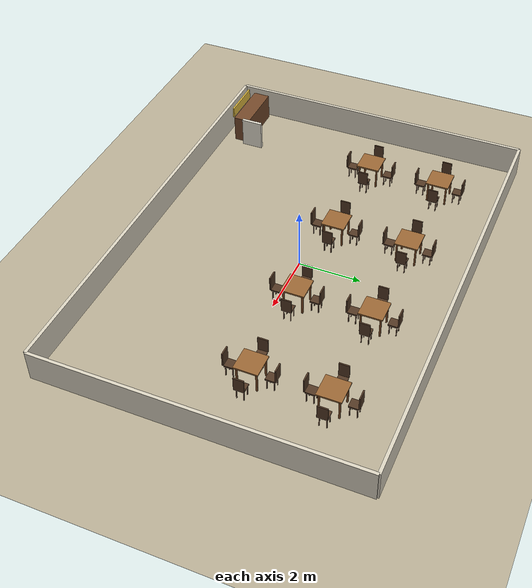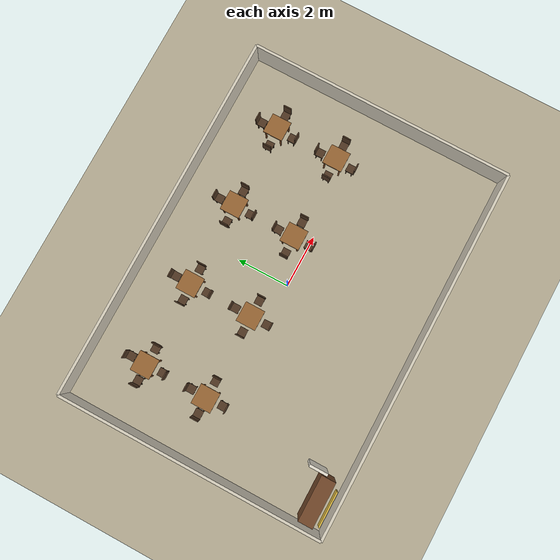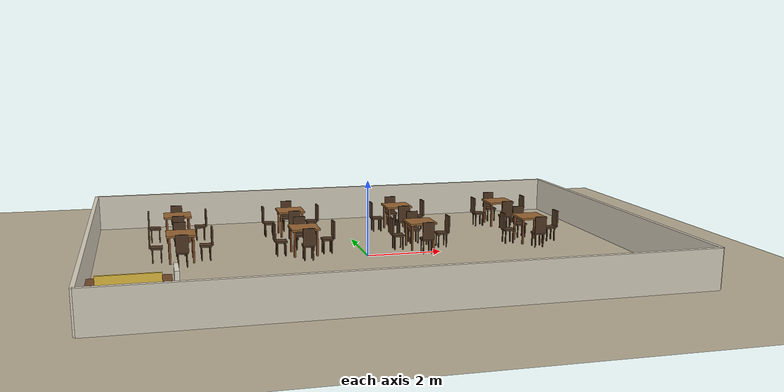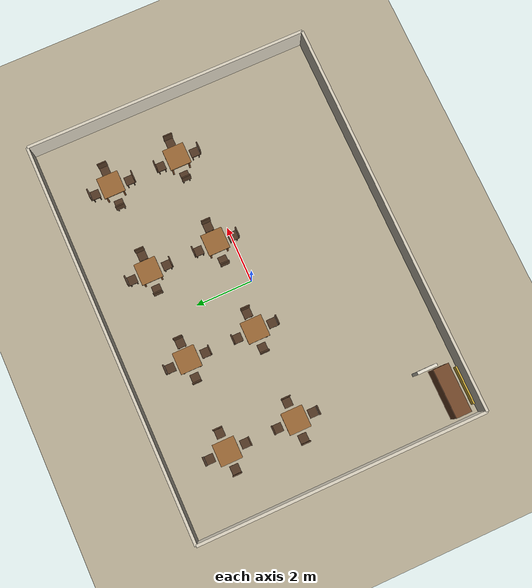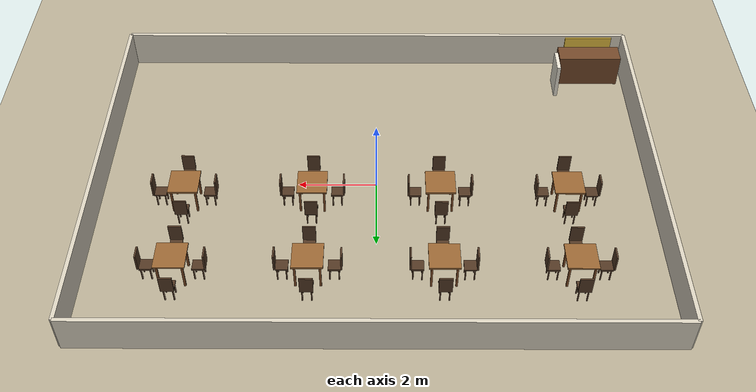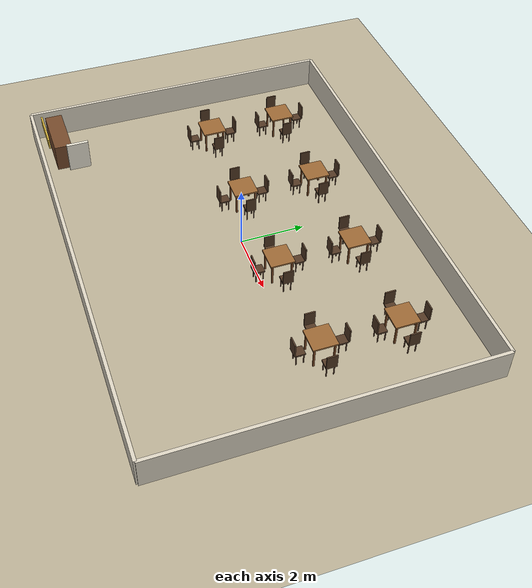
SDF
<?xml version="1.0" ?>
<sdf version="1.9">
  <world name="restaurant">
    <physics name="1ms" type="ignored">
      <max_step_size>0.001</max_step_size>
      <real_time_factor>1.0</real_time_factor>
    </physics>

    <plugin filename="gz-sim-physics-system" name="gz::sim::systems::Physics"/>
    <plugin filename="gz-sim-scene-broadcaster-system" name="gz::sim::systems::SceneBroadcaster"/>
    <plugin filename="gz-sim-user-commands-system" name="gz::sim::systems::UserCommands"/>
    <plugin filename="gz-sim-sensors-system" name="gz::sim::systems::Sensors">
      <render_engine>ogre2</render_engine>
    </plugin>

    <light type="directional" name="sun">
      <cast_shadows>true</cast_shadows>
      <pose>0 0 12 0 0 0</pose>
      <diffuse>0.9 0.9 0.85 1</diffuse>
      <specular>0.3 0.3 0.3 1</specular>
      <direction>-0.3 0.1 -0.9</direction>
    </light>

    <model name="ground">
      <static>true</static>
      <link name="link">
        <collision name="collision">
          <geometry>
            <plane>
              <normal>0 0 1</normal>
              <size>16 12</size>
            </plane>
          </geometry>
        </collision>
        <visual name="visual">
          <geometry>
            <plane>
              <normal>0 0 1</normal>
              <size>16 12</size>
            </plane>
          </geometry>
          <material>
            <ambient>0.62 0.58 0.50 1</ambient>
            <diffuse>0.72 0.68 0.58 1</diffuse>
          </material>
        </visual>
      </link>
    </model>

    <model name="wall_north">
      <static>true</static>
      <pose>0 5.05 0.5 0 0 0</pose>
      <link name="link">
        <collision name="c">
          <geometry><box><size>14.1 0.1 1.0</size></box></geometry>
        </collision>
        <visual name="v">
          <geometry><box><size>14.1 0.1 1.0</size></box></geometry>
          <material>
            <ambient>0.85 0.82 0.75 1</ambient>
            <diffuse>0.85 0.82 0.75 1</diffuse>
          </material>
        </visual>
      </link>
    </model>

    <model name="wall_south">
      <static>true</static>
      <pose>0 -5.05 0.5 0 0 0</pose>
      <link name="link">
        <collision name="c">
          <geometry><box><size>14.1 0.1 1.0</size></box></geometry>
        </collision>
        <visual name="v">
          <geometry><box><size>14.1 0.1 1.0</size></box></geometry>
          <material>
            <ambient>0.85 0.82 0.75 1</ambient>
            <diffuse>0.85 0.82 0.75 1</diffuse>
          </material>
        </visual>
      </link>
    </model>

    <model name="wall_east">
      <static>true</static>
      <pose>7.05 0 0.5 0 0 0</pose>
      <link name="link">
        <collision name="c">
          <geometry><box><size>0.1 10.1 1.0</size></box></geometry>
        </collision>
        <visual name="v">
          <geometry><box><size>0.1 10.1 1.0</size></box></geometry>
          <material>
            <ambient>0.85 0.82 0.75 1</ambient>
            <diffuse>0.85 0.82 0.75 1</diffuse>
          </material>
        </visual>
      </link>
    </model>

    <model name="wall_west">
      <static>true</static>
      <pose>-7.05 0 0.5 0 0 0</pose>
      <link name="link">
        <collision name="c">
          <geometry><box><size>0.1 10.1 1.0</size></box></geometry>
        </collision>
        <visual name="v">
          <geometry><box><size>0.1 10.1 1.0</size></box></geometry>
          <material>
            <ambient>0.85 0.82 0.75 1</ambient>
            <diffuse>0.85 0.82 0.75 1</diffuse>
          </material>
        </visual>
      </link>
    </model>

    <!-- Kitchen counter -->
    <model name="kitchen_counter">
      <static>true</static>
      <pose>-6.00 -4.35 0.45 0 0 0</pose>
      <link name="link">
        <collision name="c">
          <geometry><box><size>1.70 0.55 0.90</size></box></geometry>
        </collision>
        <visual name="v">
          <geometry><box><size>1.70 0.55 0.90</size></box></geometry>
          <material>
            <ambient>0.40 0.25 0.15 1</ambient>
            <diffuse>0.45 0.28 0.16 1</diffuse>
          </material>
        </visual>
      </link>
    </model>

    <!-- White kitchen wall: shortened so robot can stand behind it and still exit -->
    <model name="kitchen_wall">
      <static>true</static>
      <pose>-5.05 -3.90 0.50 0 0 0</pose>
      <link name="link">
        <collision name="c">
          <geometry><box><size>0.10 0.70 1.00</size></box></geometry>
        </collision>
        <visual name="v">
          <geometry><box><size>0.10 0.70 1.00</size></box></geometry>
          <material>
            <ambient>0.85 0.82 0.75 1</ambient>
            <diffuse>0.90 0.88 0.82 1</diffuse>
          </material>
        </visual>
      </link>
    </model>

    <model name="kitchen_sign">
      <static>true</static>
      <pose>-6.00 -4.75 0.95 0 0 0</pose>
      <link name="link">
        <collision name="c">
          <geometry><box><size>1.30 0.05 0.35</size></box></geometry>
        </collision>
        <visual name="v">
          <geometry><box><size>1.30 0.05 0.35</size></box></geometry>
          <material>
            <ambient>0.90 0.75 0.25 1</ambient>
            <diffuse>0.90 0.75 0.25 1</diffuse>
          </material>
        </visual>
      </link>
    </model>

    <model name="table_1">
      <static>true</static>
      <pose>-4.800 3.000 0 0 0 0</pose>
      <link name="link">
        <collision name="top_c">
          <pose>0 0 0.72 0 0 0</pose>
          <geometry><box><size>0.75 0.75 0.05</size></box></geometry>
        </collision>
        <visual name="top_v">
          <pose>0 0 0.72 0 0 0</pose>
          <geometry><box><size>0.75 0.75 0.05</size></box></geometry>
          <material>
            <ambient>0.50 0.30 0.15 1</ambient>
            <diffuse>0.60 0.40 0.20 1</diffuse>
          </material>
        </visual>

        <collision name="leg1_c">
          <pose>0.30 0.30 0.36 0 0 0</pose>
          <geometry><box><size>0.05 0.05 0.72</size></box></geometry>
        </collision>
        <visual name="leg1_v">
          <pose>0.30 0.30 0.36 0 0 0</pose>
          <geometry><box><size>0.05 0.05 0.72</size></box></geometry>
          <material>
            <ambient>0.40 0.25 0.10 1</ambient>
            <diffuse>0.50 0.30 0.15 1</diffuse>
          </material>
        </visual>

        <collision name="leg2_c">
          <pose>-0.30 0.30 0.36 0 0 0</pose>
          <geometry><box><size>0.05 0.05 0.72</size></box></geometry>
        </collision>
        <visual name="leg2_v">
          <pose>-0.30 0.30 0.36 0 0 0</pose>
          <geometry><box><size>0.05 0.05 0.72</size></box></geometry>
          <material>
            <ambient>0.40 0.25 0.10 1</ambient>
            <diffuse>0.50 0.30 0.15 1</diffuse>
          </material>
        </visual>

        <collision name="leg3_c">
          <pose>0.30 -0.30 0.36 0 0 0</pose>
          <geometry><box><size>0.05 0.05 0.72</size></box></geometry>
        </collision>
        <visual name="leg3_v">
          <pose>0.30 -0.30 0.36 0 0 0</pose>
          <geometry><box><size>0.05 0.05 0.72</size></box></geometry>
          <material>
            <ambient>0.40 0.25 0.10 1</ambient>
            <diffuse>0.50 0.30 0.15 1</diffuse>
          </material>
        </visual>

        <collision name="leg4_c">
          <pose>-0.30 -0.30 0.36 0 0 0</pose>
          <geometry><box><size>0.05 0.05 0.72</size></box></geometry>
        </collision>
        <visual name="leg4_v">
          <pose>-0.30 -0.30 0.36 0 0 0</pose>
          <geometry><box><size>0.05 0.05 0.72</size></box></geometry>
          <material>
            <ambient>0.40 0.25 0.10 1</ambient>
            <diffuse>0.50 0.30 0.15 1</diffuse>
          </material>
        </visual>
      </link>
    </model>

    <model name="chair_1_north">
      <static>true</static>
      <pose>-4.800 3.620 0 0 0 3.14159</pose>
      <link name="link">
        <collision name="seat_c">
          <pose>0 0 0.38 0 0 0</pose>
          <geometry><box><size>0.30 0.30 0.05</size></box></geometry>
        </collision>
        <visual name="seat_v">
          <pose>0 0 0.38 0 0 0</pose>
          <geometry><box><size>0.30 0.30 0.05</size></box></geometry>
          <material>
            <ambient>0.25 0.18 0.12 1</ambient>
            <diffuse>0.32 0.22 0.14 1</diffuse>
          </material>
        </visual>

        <collision name="back_c">
          <pose>0 -0.17 0.63 0 0 0</pose>
          <geometry><box><size>0.32 0.04 0.46</size></box></geometry>
        </collision>
        <visual name="back_v">
          <pose>0 -0.17 0.63 0 0 0</pose>
          <geometry><box><size>0.32 0.04 0.46</size></box></geometry>
          <material>
            <ambient>0.25 0.18 0.12 1</ambient>
            <diffuse>0.32 0.22 0.14 1</diffuse>
          </material>
        </visual>

        <collision name="leg1_c">
          <pose>0.11 0.11 0.19 0 0 0</pose>
          <geometry><box><size>0.03 0.03 0.38</size></box></geometry>
        </collision>
        <visual name="leg1_v">
          <pose>0.11 0.11 0.19 0 0 0</pose>
          <geometry><box><size>0.03 0.03 0.38</size></box></geometry>
          <material>
            <ambient>0.20 0.12 0.08 1</ambient>
            <diffuse>0.28 0.18 0.10 1</diffuse>
          </material>
        </visual>

        <collision name="leg2_c">
          <pose>-0.11 0.11 0.19 0 0 0</pose>
          <geometry><box><size>0.03 0.03 0.38</size></box></geometry>
        </collision>
        <visual name="leg2_v">
          <pose>-0.11 0.11 0.19 0 0 0</pose>
          <geometry><box><size>0.03 0.03 0.38</size></box></geometry>
          <material>
            <ambient>0.20 0.12 0.08 1</ambient>
            <diffuse>0.28 0.18 0.10 1</diffuse>
          </material>
        </visual>

        <collision name="leg3_c">
          <pose>0.11 -0.11 0.19 0 0 0</pose>
          <geometry><box><size>0.03 0.03 0.38</size></box></geometry>
        </collision>
        <visual name="leg3_v">
          <pose>0.11 -0.11 0.19 0 0 0</pose>
          <geometry><box><size>0.03 0.03 0.38</size></box></geometry>
          <material>
            <ambient>0.20 0.12 0.08 1</ambient>
            <diffuse>0.28 0.18 0.10 1</diffuse>
          </material>
        </visual>

        <collision name="leg4_c">
          <pose>-0.11 -0.11 0.19 0 0 0</pose>
          <geometry><box><size>0.03 0.03 0.38</size></box></geometry>
        </collision>
        <visual name="leg4_v">
          <pose>-0.11 -0.11 0.19 0 0 0</pose>
          <geometry><box><size>0.03 0.03 0.38</size></box></geometry>
          <material>
            <ambient>0.20 0.12 0.08 1</ambient>
            <diffuse>0.28 0.18 0.10 1</diffuse>
          </material>
        </visual>
      </link>
    </model>

    <model name="chair_1_south">
      <static>true</static>
      <pose>-4.800 2.380 0 0 0 0.00000</pose>
      <link name="link">
        <collision name="seat_c">
          <pose>0 0 0.38 0 0 0</pose>
          <geometry><box><size>0.30 0.30 0.05</size></box></geometry>
        </collision>
        <visual name="seat_v">
          <pose>0 0 0.38 0 0 0</pose>
          <geometry><box><size>0.30 0.30 0.05</size></box></geometry>
          <material>
            <ambient>0.25 0.18 0.12 1</ambient>
            <diffuse>0.32 0.22 0.14 1</diffuse>
          </material>
        </visual>

        <collision name="back_c">
          <pose>0 -0.17 0.63 0 0 0</pose>
          <geometry><box><size>0.32 0.04 0.46</size></box></geometry>
        </collision>
        <visual name="back_v">
          <pose>0 -0.17 0.63 0 0 0</pose>
          <geometry><box><size>0.32 0.04 0.46</size></box></geometry>
          <material>
            <ambient>0.25 0.18 0.12 1</ambient>
            <diffuse>0.32 0.22 0.14 1</diffuse>
          </material>
        </visual>

        <collision name="leg1_c">
          <pose>0.11 0.11 0.19 0 0 0</pose>
          <geometry><box><size>0.03 0.03 0.38</size></box></geometry>
        </collision>
        <visual name="leg1_v">
          <pose>0.11 0.11 0.19 0 0 0</pose>
          <geometry><box><size>0.03 0.03 0.38</size></box></geometry>
          <material>
            <ambient>0.20 0.12 0.08 1</ambient>
            <diffuse>0.28 0.18 0.10 1</diffuse>
          </material>
        </visual>

        <collision name="leg2_c">
          <pose>-0.11 0.11 0.19 0 0 0</pose>
          <geometry><box><size>0.03 0.03 0.38</size></box></geometry>
        </collision>
        <visual name="leg2_v">
          <pose>-0.11 0.11 0.19 0 0 0</pose>
          <geometry><box><size>0.03 0.03 0.38</size></box></geometry>
          <material>
            <ambient>0.20 0.12 0.08 1</ambient>
            <diffuse>0.28 0.18 0.10 1</diffuse>
          </material>
        </visual>

        <collision name="leg3_c">
          <pose>0.11 -0.11 0.19 0 0 0</pose>
          <geometry><box><size>0.03 0.03 0.38</size></box></geometry>
        </collision>
        <visual name="leg3_v">
          <pose>0.11 -0.11 0.19 0 0 0</pose>
          <geometry><box><size>0.03 0.03 0.38</size></box></geometry>
          <material>
            <ambient>0.20 0.12 0.08 1</ambient>
            <diffuse>0.28 0.18 0.10 1</diffuse>
          </material>
        </visual>

        <collision name="leg4_c">
          <pose>-0.11 -0.11 0.19 0 0 0</pose>
          <geometry><box><size>0.03 0.03 0.38</size></box></geometry>
        </collision>
        <visual name="leg4_v">
          <pose>-0.11 -0.11 0.19 0 0 0</pose>
          <geometry><box><size>0.03 0.03 0.38</size></box></geometry>
          <material>
            <ambient>0.20 0.12 0.08 1</ambient>
            <diffuse>0.28 0.18 0.10 1</diffuse>
          </material>
        </visual>
      </link>
    </model>

    <model name="chair_1_east">
      <static>true</static>
      <pose>-4.180 3.000 0 0 0 1.57080</pose>
      <link name="link">
        <collision name="seat_c">
          <pose>0 0 0.38 0 0 0</pose>
          <geometry><box><size>0.30 0.30 0.05</size></box></geometry>
        </collision>
        <visual name="seat_v">
          <pose>0 0 0.38 0 0 0</pose>
          <geometry><box><size>0.30 0.30 0.05</size></box></geometry>
          <material>
            <ambient>0.25 0.18 0.12 1</ambient>
            <diffuse>0.32 0.22 0.14 1</diffuse>
          </material>
        </visual>

        <collision name="back_c">
          <pose>0 -0.17 0.63 0 0 0</pose>
          <geometry><box><size>0.32 0.04 0.46</size></box></geometry>
        </collision>
        <visual name="back_v">
          <pose>0 -0.17 0.63 0 0 0</pose>
          <geometry><box><size>0.32 0.04 0.46</size></box></geometry>
          <material>
            <ambient>0.25 0.18 0.12 1</ambient>
            <diffuse>0.32 0.22 0.14 1</diffuse>
          </material>
        </visual>

        <collision name="leg1_c">
          <pose>0.11 0.11 0.19 0 0 0</pose>
          <geometry><box><size>0.03 0.03 0.38</size></box></geometry>
        </collision>
        <visual name="leg1_v">
          <pose>0.11 0.11 0.19 0 0 0</pose>
          <geometry><box><size>0.03 0.03 0.38</size></box></geometry>
          <material>
            <ambient>0.20 0.12 0.08 1</ambient>
            <diffuse>0.28 0.18 0.10 1</diffuse>
          </material>
        </visual>

        <collision name="leg2_c">
          <pose>-0.11 0.11 0.19 0 0 0</pose>
          <geometry><box><size>0.03 0.03 0.38</size></box></geometry>
        </collision>
        <visual name="leg2_v">
          <pose>-0.11 0.11 0.19 0 0 0</pose>
          <geometry><box><size>0.03 0.03 0.38</size></box></geometry>
          <material>
            <ambient>0.20 0.12 0.08 1</ambient>
            <diffuse>0.28 0.18 0.10 1</diffuse>
          </material>
        </visual>

        <collision name="leg3_c">
          <pose>0.11 -0.11 0.19 0 0 0</pose>
          <geometry><box><size>0.03 0.03 0.38</size></box></geometry>
        </collision>
        <visual name="leg3_v">
          <pose>0.11 -0.11 0.19 0 0 0</pose>
          <geometry><box><size>0.03 0.03 0.38</size></box></geometry>
          <material>
            <ambient>0.20 0.12 0.08 1</ambient>
            <diffuse>0.28 0.18 0.10 1</diffuse>
          </material>
        </visual>

        <collision name="leg4_c">
          <pose>-0.11 -0.11 0.19 0 0 0</pose>
          <geometry><box><size>0.03 0.03 0.38</size></box></geometry>
        </collision>
        <visual name="leg4_v">
          <pose>-0.11 -0.11 0.19 0 0 0</pose>
          <geometry><box><size>0.03 0.03 0.38</size></box></geometry>
          <material>
            <ambient>0.20 0.12 0.08 1</ambient>
            <diffuse>0.28 0.18 0.10 1</diffuse>
          </material>
        </visual>
      </link>
    </model>

    <model name="chair_1_west">
      <static>true</static>
      <pose>-5.420 3.000 0 0 0 -1.57080</pose>
      <link name="link">
        <collision name="seat_c">
          <pose>0 0 0.38 0 0 0</pose>
          <geometry><box><size>0.30 0.30 0.05</size></box></geometry>
        </collision>
        <visual name="seat_v">
          <pose>0 0 0.38 0 0 0</pose>
          <geometry><box><size>0.30 0.30 0.05</size></box></geometry>
          <material>
            <ambient>0.25 0.18 0.12 1</ambient>
            <diffuse>0.32 0.22 0.14 1</diffuse>
          </material>
        </visual>

        <collision name="back_c">
          <pose>0 -0.17 0.63 0 0 0</pose>
          <geometry><box><size>0.32 0.04 0.46</size></box></geometry>
        </collision>
        <visual name="back_v">
          <pose>0 -0.17 0.63 0 0 0</pose>
          <geometry><box><size>0.32 0.04 0.46</size></box></geometry>
          <material>
            <ambient>0.25 0.18 0.12 1</ambient>
            <diffuse>0.32 0.22 0.14 1</diffuse>
          </material>
        </visual>

        <collision name="leg1_c">
          <pose>0.11 0.11 0.19 0 0 0</pose>
          <geometry><box><size>0.03 0.03 0.38</size></box></geometry>
        </collision>
        <visual name="leg1_v">
          <pose>0.11 0.11 0.19 0 0 0</pose>
          <geometry><box><size>0.03 0.03 0.38</size></box></geometry>
          <material>
            <ambient>0.20 0.12 0.08 1</ambient>
            <diffuse>0.28 0.18 0.10 1</diffuse>
          </material>
        </visual>

        <collision name="leg2_c">
          <pose>-0.11 0.11 0.19 0 0 0</pose>
          <geometry><box><size>0.03 0.03 0.38</size></box></geometry>
        </collision>
        <visual name="leg2_v">
          <pose>-0.11 0.11 0.19 0 0 0</pose>
          <geometry><box><size>0.03 0.03 0.38</size></box></geometry>
          <material>
            <ambient>0.20 0.12 0.08 1</ambient>
            <diffuse>0.28 0.18 0.10 1</diffuse>
          </material>
        </visual>

        <collision name="leg3_c">
          <pose>0.11 -0.11 0.19 0 0 0</pose>
          <geometry><box><size>0.03 0.03 0.38</size></box></geometry>
        </collision>
        <visual name="leg3_v">
          <pose>0.11 -0.11 0.19 0 0 0</pose>
          <geometry><box><size>0.03 0.03 0.38</size></box></geometry>
          <material>
            <ambient>0.20 0.12 0.08 1</ambient>
            <diffuse>0.28 0.18 0.10 1</diffuse>
          </material>
        </visual>

        <collision name="leg4_c">
          <pose>-0.11 -0.11 0.19 0 0 0</pose>
          <geometry><box><size>0.03 0.03 0.38</size></box></geometry>
        </collision>
        <visual name="leg4_v">
          <pose>-0.11 -0.11 0.19 0 0 0</pose>
          <geometry><box><size>0.03 0.03 0.38</size></box></geometry>
          <material>
            <ambient>0.20 0.12 0.08 1</ambient>
            <diffuse>0.28 0.18 0.10 1</diffuse>
          </material>
        </visual>
      </link>
    </model>

    <model name="table_2">
      <static>true</static>
      <pose>-1.600 3.000 0 0 0 0</pose>
      <link name="link">
        <collision name="top_c">
          <pose>0 0 0.72 0 0 0</pose>
          <geometry><box><size>0.75 0.75 0.05</size></box></geometry>
        </collision>
        <visual name="top_v">
          <pose>0 0 0.72 0 0 0</pose>
          <geometry><box><size>0.75 0.75 0.05</size></box></geometry>
          <material>
            <ambient>0.50 0.30 0.15 1</ambient>
            <diffuse>0.60 0.40 0.20 1</diffuse>
          </material>
        </visual>

        <collision name="leg1_c">
          <pose>0.30 0.30 0.36 0 0 0</pose>
          <geometry><box><size>0.05 0.05 0.72</size></box></geometry>
        </collision>
        <visual name="leg1_v">
          <pose>0.30 0.30 0.36 0 0 0</pose>
          <geometry><box><size>0.05 0.05 0.72</size></box></geometry>
          <material>
            <ambient>0.40 0.25 0.10 1</ambient>
            <diffuse>0.50 0.30 0.15 1</diffuse>
          </material>
        </visual>

        <collision name="leg2_c">
          <pose>-0.30 0.30 0.36 0 0 0</pose>
          <geometry><box><size>0.05 0.05 0.72</size></box></geometry>
        </collision>
        <visual name="leg2_v">
          <pose>-0.30 0.30 0.36 0 0 0</pose>
          <geometry><box><size>0.05 0.05 0.72</size></box></geometry>
          <material>
            <ambient>0.40 0.25 0.10 1</ambient>
            <diffuse>0.50 0.30 0.15 1</diffuse>
          </material>
        </visual>

        <collision name="leg3_c">
          <pose>0.30 -0.30 0.36 0 0 0</pose>
          <geometry><box><size>0.05 0.05 0.72</size></box></geometry>
        </collision>
        <visual name="leg3_v">
          <pose>0.30 -0.30 0.36 0 0 0</pose>
          <geometry><box><size>0.05 0.05 0.72</size></box></geometry>
          <material>
            <ambient>0.40 0.25 0.10 1</ambient>
            <diffuse>0.50 0.30 0.15 1</diffuse>
          </material>
        </visual>

        <collision name="leg4_c">
          <pose>-0.30 -0.30 0.36 0 0 0</pose>
          <geometry><box><size>0.05 0.05 0.72</size></box></geometry>
        </collision>
        <visual name="leg4_v">
          <pose>-0.30 -0.30 0.36 0 0 0</pose>
          <geometry><box><size>0.05 0.05 0.72</size></box></geometry>
          <material>
            <ambient>0.40 0.25 0.10 1</ambient>
            <diffuse>0.50 0.30 0.15 1</diffuse>
          </material>
        </visual>
      </link>
    </model>

    <model name="chair_2_north">
      <static>true</static>
      <pose>-1.600 3.620 0 0 0 3.14159</pose>
      <link name="link">
        <collision name="seat_c">
          <pose>0 0 0.38 0 0 0</pose>
          <geometry><box><size>0.30 0.30 0.05</size></box></geometry>
        </collision>
        <visual name="seat_v">
          <pose>0 0 0.38 0 0 0</pose>
          <geometry><box><size>0.30 0.30 0.05</size></box></geometry>
          <material>
            <ambient>0.25 0.18 0.12 1</ambient>
            <diffuse>0.32 0.22 0.14 1</diffuse>
          </material>
        </visual>

        <collision name="back_c">
          <pose>0 -0.17 0.63 0 0 0</pose>
          <geometry><box><size>0.32 0.04 0.46</size></box></geometry>
        </collision>
        <visual name="back_v">
          <pose>0 -0.17 0.63 0 0 0</pose>
          <geometry><box><size>0.32 0.04 0.46</size></box></geometry>
          <material>
            <ambient>0.25 0.18 0.12 1</ambient>
            <diffuse>0.32 0.22 0.14 1</diffuse>
          </material>
        </visual>

        <collision name="leg1_c">
          <pose>0.11 0.11 0.19 0 0 0</pose>
          <geometry><box><size>0.03 0.03 0.38</size></box></geometry>
        </collision>
        <visual name="leg1_v">
          <pose>0.11 0.11 0.19 0 0 0</pose>
          <geometry><box><size>0.03 0.03 0.38</size></box></geometry>
          <material>
            <ambient>0.20 0.12 0.08 1</ambient>
            <diffuse>0.28 0.18 0.10 1</diffuse>
          </material>
        </visual>

        <collision name="leg2_c">
          <pose>-0.11 0.11 0.19 0 0 0</pose>
          <geometry><box><size>0.03 0.03 0.38</size></box></geometry>
        </collision>
        <visual name="leg2_v">
          <pose>-0.11 0.11 0.19 0 0 0</pose>
          <geometry><box><size>0.03 0.03 0.38</size></box></geometry>
          <material>
            <ambient>0.20 0.12 0.08 1</ambient>
            <diffuse>0.28 0.18 0.10 1</diffuse>
          </material>
        </visual>

        <collision name="leg3_c">
          <pose>0.11 -0.11 0.19 0 0 0</pose>
          <geometry><box><size>0.03 0.03 0.38</size></box></geometry>
        </collision>
        <visual name="leg3_v">
          <pose>0.11 -0.11 0.19 0 0 0</pose>
          <geometry><box><size>0.03 0.03 0.38</size></box></geometry>
          <material>
            <ambient>0.20 0.12 0.08 1</ambient>
            <diffuse>0.28 0.18 0.10 1</diffuse>
          </material>
        </visual>

        <collision name="leg4_c">
          <pose>-0.11 -0.11 0.19 0 0 0</pose>
          <geometry><box><size>0.03 0.03 0.38</size></box></geometry>
        </collision>
        <visual name="leg4_v">
          <pose>-0.11 -0.11 0.19 0 0 0</pose>
          <geometry><box><size>0.03 0.03 0.38</size></box></geometry>
          <material>
            <ambient>0.20 0.12 0.08 1</ambient>
            <diffuse>0.28 0.18 0.10 1</diffuse>
          </material>
        </visual>
      </link>
    </model>

    <model name="chair_2_south">
      <static>true</static>
      <pose>-1.600 2.380 0 0 0 0.00000</pose>
      <link name="link">
        <collision name="seat_c">
          <pose>0 0 0.38 0 0 0</pose>
          <geometry><box><size>0.30 0.30 0.05</size></box></geometry>
        </collision>
        <visual name="seat_v">
          <pose>0 0 0.38 0 0 0</pose>
          <geometry><box><size>0.30 0.30 0.05</size></box></geometry>
          <material>
            <ambient>0.25 0.18 0.12 1</ambient>
            <diffuse>0.32 0.22 0.14 1</diffuse>
          </material>
        </visual>

        <collision name="back_c">
          <pose>0 -0.17 0.63 0 0 0</pose>
          <geometry><box><size>0.32 0.04 0.46</size></box></geometry>
        </collision>
        <visual name="back_v">
          <pose>0 -0.17 0.63 0 0 0</pose>
          <geometry><box><size>0.32 0.04 0.46</size></box></geometry>
          <material>
            <ambient>0.25 0.18 0.12 1</ambient>
            <diffuse>0.32 0.22 0.14 1</diffuse>
          </material>
        </visual>

        <collision name="leg1_c">
          <pose>0.11 0.11 0.19 0 0 0</pose>
          <geometry><box><size>0.03 0.03 0.38</size></box></geometry>
        </collision>
        <visual name="leg1_v">
          <pose>0.11 0.11 0.19 0 0 0</pose>
          <geometry><box><size>0.03 0.03 0.38</size></box></geometry>
          <material>
            <ambient>0.20 0.12 0.08 1</ambient>
            <diffuse>0.28 0.18 0.10 1</diffuse>
          </material>
        </visual>

        <collision name="leg2_c">
          <pose>-0.11 0.11 0.19 0 0 0</pose>
          <geometry><box><size>0.03 0.03 0.38</size></box></geometry>
        </collision>
        <visual name="leg2_v">
          <pose>-0.11 0.11 0.19 0 0 0</pose>
          <geometry><box><size>0.03 0.03 0.38</size></box></geometry>
          <material>
            <ambient>0.20 0.12 0.08 1</ambient>
            <diffuse>0.28 0.18 0.10 1</diffuse>
          </material>
        </visual>

        <collision name="leg3_c">
          <pose>0.11 -0.11 0.19 0 0 0</pose>
          <geometry><box><size>0.03 0.03 0.38</size></box></geometry>
        </collision>
        <visual name="leg3_v">
          <pose>0.11 -0.11 0.19 0 0 0</pose>
          <geometry><box><size>0.03 0.03 0.38</size></box></geometry>
          <material>
            <ambient>0.20 0.12 0.08 1</ambient>
            <diffuse>0.28 0.18 0.10 1</diffuse>
          </material>
        </visual>

        <collision name="leg4_c">
          <pose>-0.11 -0.11 0.19 0 0 0</pose>
          <geometry><box><size>0.03 0.03 0.38</size></box></geometry>
        </collision>
        <visual name="leg4_v">
          <pose>-0.11 -0.11 0.19 0 0 0</pose>
          <geometry><box><size>0.03 0.03 0.38</size></box></geometry>
          <material>
            <ambient>0.20 0.12 0.08 1</ambient>
            <diffuse>0.28 0.18 0.10 1</diffuse>
          </material>
        </visual>
      </link>
    </model>

    <model name="chair_2_east">
      <static>true</static>
      <pose>-0.980 3.000 0 0 0 1.57080</pose>
      <link name="link">
        <collision name="seat_c">
          <pose>0 0 0.38 0 0 0</pose>
          <geometry><box><size>0.30 0.30 0.05</size></box></geometry>
        </collision>
        <visual name="seat_v">
          <pose>0 0 0.38 0 0 0</pose>
          <geometry><box><size>0.30 0.30 0.05</size></box></geometry>
          <material>
            <ambient>0.25 0.18 0.12 1</ambient>
            <diffuse>0.32 0.22 0.14 1</diffuse>
          </material>
        </visual>

        <collision name="back_c">
          <pose>0 -0.17 0.63 0 0 0</pose>
          <geometry><box><size>0.32 0.04 0.46</size></box></geometry>
        </collision>
        <visual name="back_v">
          <pose>0 -0.17 0.63 0 0 0</pose>
          <geometry><box><size>0.32 0.04 0.46</size></box></geometry>
          <material>
            <ambient>0.25 0.18 0.12 1</ambient>
            <diffuse>0.32 0.22 0.14 1</diffuse>
          </material>
        </visual>

        <collision name="leg1_c">
          <pose>0.11 0.11 0.19 0 0 0</pose>
          <geometry><box><size>0.03 0.03 0.38</size></box></geometry>
        </collision>
        <visual name="leg1_v">
          <pose>0.11 0.11 0.19 0 0 0</pose>
          <geometry><box><size>0.03 0.03 0.38</size></box></geometry>
          <material>
            <ambient>0.20 0.12 0.08 1</ambient>
            <diffuse>0.28 0.18 0.10 1</diffuse>
          </material>
        </visual>

        <collision name="leg2_c">
          <pose>-0.11 0.11 0.19 0 0 0</pose>
          <geometry><box><size>0.03 0.03 0.38</size></box></geometry>
        </collision>
        <visual name="leg2_v">
          <pose>-0.11 0.11 0.19 0 0 0</pose>
          <geometry><box><size>0.03 0.03 0.38</size></box></geometry>
          <material>
            <ambient>0.20 0.12 0.08 1</ambient>
            <diffuse>0.28 0.18 0.10 1</diffuse>
          </material>
        </visual>

        <collision name="leg3_c">
          <pose>0.11 -0.11 0.19 0 0 0</pose>
          <geometry><box><size>0.03 0.03 0.38</size></box></geometry>
        </collision>
        <visual name="leg3_v">
          <pose>0.11 -0.11 0.19 0 0 0</pose>
          <geometry><box><size>0.03 0.03 0.38</size></box></geometry>
          <material>
            <ambient>0.20 0.12 0.08 1</ambient>
            <diffuse>0.28 0.18 0.10 1</diffuse>
          </material>
        </visual>

        <collision name="leg4_c">
          <pose>-0.11 -0.11 0.19 0 0 0</pose>
          <geometry><box><size>0.03 0.03 0.38</size></box></geometry>
        </collision>
        <visual name="leg4_v">
          <pose>-0.11 -0.11 0.19 0 0 0</pose>
          <geometry><box><size>0.03 0.03 0.38</size></box></geometry>
          <material>
            <ambient>0.20 0.12 0.08 1</ambient>
            <diffuse>0.28 0.18 0.10 1</diffuse>
          </material>
        </visual>
      </link>
    </model>

    <model name="chair_2_west">
      <static>true</static>
      <pose>-2.220 3.000 0 0 0 -1.57080</pose>
      <link name="link">
        <collision name="seat_c">
          <pose>0 0 0.38 0 0 0</pose>
          <geometry><box><size>0.30 0.30 0.05</size></box></geometry>
        </collision>
        <visual name="seat_v">
          <pose>0 0 0.38 0 0 0</pose>
          <geometry><box><size>0.30 0.30 0.05</size></box></geometry>
          <material>
            <ambient>0.25 0.18 0.12 1</ambient>
            <diffuse>0.32 0.22 0.14 1</diffuse>
          </material>
        </visual>

        <collision name="back_c">
          <pose>0 -0.17 0.63 0 0 0</pose>
          <geometry><box><size>0.32 0.04 0.46</size></box></geometry>
        </collision>
        <visual name="back_v">
          <pose>0 -0.17 0.63 0 0 0</pose>
          <geometry><box><size>0.32 0.04 0.46</size></box></geometry>
          <material>
            <ambient>0.25 0.18 0.12 1</ambient>
            <diffuse>0.32 0.22 0.14 1</diffuse>
          </material>
        </visual>

        <collision name="leg1_c">
          <pose>0.11 0.11 0.19 0 0 0</pose>
          <geometry><box><size>0.03 0.03 0.38</size></box></geometry>
        </collision>
        <visual name="leg1_v">
          <pose>0.11 0.11 0.19 0 0 0</pose>
          <geometry><box><size>0.03 0.03 0.38</size></box></geometry>
          <material>
            <ambient>0.20 0.12 0.08 1</ambient>
            <diffuse>0.28 0.18 0.10 1</diffuse>
          </material>
        </visual>

        <collision name="leg2_c">
          <pose>-0.11 0.11 0.19 0 0 0</pose>
          <geometry><box><size>0.03 0.03 0.38</size></box></geometry>
        </collision>
        <visual name="leg2_v">
          <pose>-0.11 0.11 0.19 0 0 0</pose>
          <geometry><box><size>0.03 0.03 0.38</size></box></geometry>
          <material>
            <ambient>0.20 0.12 0.08 1</ambient>
            <diffuse>0.28 0.18 0.10 1</diffuse>
          </material>
        </visual>

        <collision name="leg3_c">
          <pose>0.11 -0.11 0.19 0 0 0</pose>
          <geometry><box><size>0.03 0.03 0.38</size></box></geometry>
        </collision>
        <visual name="leg3_v">
          <pose>0.11 -0.11 0.19 0 0 0</pose>
          <geometry><box><size>0.03 0.03 0.38</size></box></geometry>
          <material>
            <ambient>0.20 0.12 0.08 1</ambient>
            <diffuse>0.28 0.18 0.10 1</diffuse>
          </material>
        </visual>

        <collision name="leg4_c">
          <pose>-0.11 -0.11 0.19 0 0 0</pose>
          <geometry><box><size>0.03 0.03 0.38</size></box></geometry>
        </collision>
        <visual name="leg4_v">
          <pose>-0.11 -0.11 0.19 0 0 0</pose>
          <geometry><box><size>0.03 0.03 0.38</size></box></geometry>
          <material>
            <ambient>0.20 0.12 0.08 1</ambient>
            <diffuse>0.28 0.18 0.10 1</diffuse>
          </material>
        </visual>
      </link>
    </model>

    <model name="table_3">
      <static>true</static>
      <pose>1.600 3.000 0 0 0 0</pose>
      <link name="link">
        <collision name="top_c">
          <pose>0 0 0.72 0 0 0</pose>
          <geometry><box><size>0.75 0.75 0.05</size></box></geometry>
        </collision>
        <visual name="top_v">
          <pose>0 0 0.72 0 0 0</pose>
          <geometry><box><size>0.75 0.75 0.05</size></box></geometry>
          <material>
            <ambient>0.50 0.30 0.15 1</ambient>
            <diffuse>0.60 0.40 0.20 1</diffuse>
          </material>
        </visual>

        <collision name="leg1_c">
          <pose>0.30 0.30 0.36 0 0 0</pose>
          <geometry><box><size>0.05 0.05 0.72</size></box></geometry>
        </collision>
        <visual name="leg1_v">
          <pose>0.30 0.30 0.36 0 0 0</pose>
          <geometry><box><size>0.05 0.05 0.72</size></box></geometry>
          <material>
            <ambient>0.40 0.25 0.10 1</ambient>
            <diffuse>0.50 0.30 0.15 1</diffuse>
          </material>
        </visual>

        <collision name="leg2_c">
          <pose>-0.30 0.30 0.36 0 0 0</pose>
          <geometry><box><size>0.05 0.05 0.72</size></box></geometry>
        </collision>
        <visual name="leg2_v">
          <pose>-0.30 0.30 0.36 0 0 0</pose>
          <geometry><box><size>0.05 0.05 0.72</size></box></geometry>
          <material>
            <ambient>0.40 0.25 0.10 1</ambient>
            <diffuse>0.50 0.30 0.15 1</diffuse>
          </material>
        </visual>

        <collision name="leg3_c">
          <pose>0.30 -0.30 0.36 0 0 0</pose>
          <geometry><box><size>0.05 0.05 0.72</size></box></geometry>
        </collision>
        <visual name="leg3_v">
          <pose>0.30 -0.30 0.36 0 0 0</pose>
          <geometry><box><size>0.05 0.05 0.72</size></box></geometry>
          <material>
            <ambient>0.40 0.25 0.10 1</ambient>
            <diffuse>0.50 0.30 0.15 1</diffuse>
          </material>
        </visual>

        <collision name="leg4_c">
          <pose>-0.30 -0.30 0.36 0 0 0</pose>
          <geometry><box><size>0.05 0.05 0.72</size></box></geometry>
        </collision>
        <visual name="leg4_v">
          <pose>-0.30 -0.30 0.36 0 0 0</pose>
          <geometry><box><size>0.05 0.05 0.72</size></box></geometry>
          <material>
            <ambient>0.40 0.25 0.10 1</ambient>
            <diffuse>0.50 0.30 0.15 1</diffuse>
          </material>
        </visual>
      </link>
    </model>

    <model name="chair_3_north">
      <static>true</static>
      <pose>1.600 3.620 0 0 0 3.14159</pose>
      <link name="link">
        <collision name="seat_c">
          <pose>0 0 0.38 0 0 0</pose>
          <geometry><box><size>0.30 0.30 0.05</size></box></geometry>
        </collision>
        <visual name="seat_v">
          <pose>0 0 0.38 0 0 0</pose>
          <geometry><box><size>0.30 0.30 0.05</size></box></geometry>
          <material>
            <ambient>0.25 0.18 0.12 1</ambient>
            <diffuse>0.32 0.22 0.14 1</diffuse>
          </material>
        </visual>

        <collision name="back_c">
          <pose>0 -0.17 0.63 0 0 0</pose>
          <geometry><box><size>0.32 0.04 0.46</size></box></geometry>
        </collision>
        <visual name="back_v">
          <pose>0 -0.17 0.63 0 0 0</pose>
          <geometry><box><size>0.32 0.04 0.46</size></box></geometry>
          <material>
            <ambient>0.25 0.18 0.12 1</ambient>
            <diffuse>0.32 0.22 0.14 1</diffuse>
          </material>
        </visual>

        <collision name="leg1_c">
          <pose>0.11 0.11 0.19 0 0 0</pose>
          <geometry><box><size>0.03 0.03 0.38</size></box></geometry>
        </collision>
        <visual name="leg1_v">
          <pose>0.11 0.11 0.19 0 0 0</pose>
          <geometry><box><size>0.03 0.03 0.38</size></box></geometry>
          <material>
            <ambient>0.20 0.12 0.08 1</ambient>
            <diffuse>0.28 0.18 0.10 1</diffuse>
          </material>
        </visual>

        <collision name="leg2_c">
          <pose>-0.11 0.11 0.19 0 0 0</pose>
          <geometry><box><size>0.03 0.03 0.38</size></box></geometry>
        </collision>
        <visual name="leg2_v">
          <pose>-0.11 0.11 0.19 0 0 0</pose>
          <geometry><box><size>0.03 0.03 0.38</size></box></geometry>
          <material>
            <ambient>0.20 0.12 0.08 1</ambient>
            <diffuse>0.28 0.18 0.10 1</diffuse>
          </material>
        </visual>

        <collision name="leg3_c">
          <pose>0.11 -0.11 0.19 0 0 0</pose>
          <geometry><box><size>0.03 0.03 0.38</size></box></geometry>
        </collision>
        <visual name="leg3_v">
          <pose>0.11 -0.11 0.19 0 0 0</pose>
          <geometry><box><size>0.03 0.03 0.38</size></box></geometry>
          <material>
            <ambient>0.20 0.12 0.08 1</ambient>
            <diffuse>0.28 0.18 0.10 1</diffuse>
          </material>
        </visual>

        <collision name="leg4_c">
          <pose>-0.11 -0.11 0.19 0 0 0</pose>
          <geometry><box><size>0.03 0.03 0.38</size></box></geometry>
        </collision>
        <visual name="leg4_v">
          <pose>-0.11 -0.11 0.19 0 0 0</pose>
          <geometry><box><size>0.03 0.03 0.38</size></box></geometry>
          <material>
            <ambient>0.20 0.12 0.08 1</ambient>
            <diffuse>0.28 0.18 0.10 1</diffuse>
          </material>
        </visual>
      </link>
    </model>

    <model name="chair_3_south">
      <static>true</static>
      <pose>1.600 2.380 0 0 0 0.00000</pose>
      <link name="link">
        <collision name="seat_c">
          <pose>0 0 0.38 0 0 0</pose>
          <geometry><box><size>0.30 0.30 0.05</size></box></geometry>
        </collision>
        <visual name="seat_v">
          <pose>0 0 0.38 0 0 0</pose>
          <geometry><box><size>0.30 0.30 0.05</size></box></geometry>
          <material>
            <ambient>0.25 0.18 0.12 1</ambient>
            <diffuse>0.32 0.22 0.14 1</diffuse>
          </material>
        </visual>

        <collision name="back_c">
          <pose>0 -0.17 0.63 0 0 0</pose>
          <geometry><box><size>0.32 0.04 0.46</size></box></geometry>
        </collision>
        <visual name="back_v">
          <pose>0 -0.17 0.63 0 0 0</pose>
          <geometry><box><size>0.32 0.04 0.46</size></box></geometry>
          <material>
            <ambient>0.25 0.18 0.12 1</ambient>
            <diffuse>0.32 0.22 0.14 1</diffuse>
          </material>
        </visual>

        <collision name="leg1_c">
          <pose>0.11 0.11 0.19 0 0 0</pose>
          <geometry><box><size>0.03 0.03 0.38</size></box></geometry>
        </collision>
        <visual name="leg1_v">
          <pose>0.11 0.11 0.19 0 0 0</pose>
          <geometry><box><size>0.03 0.03 0.38</size></box></geometry>
          <material>
            <ambient>0.20 0.12 0.08 1</ambient>
            <diffuse>0.28 0.18 0.10 1</diffuse>
          </material>
        </visual>

        <collision name="leg2_c">
          <pose>-0.11 0.11 0.19 0 0 0</pose>
          <geometry><box><size>0.03 0.03 0.38</size></box></geometry>
        </collision>
        <visual name="leg2_v">
          <pose>-0.11 0.11 0.19 0 0 0</pose>
          <geometry><box><size>0.03 0.03 0.38</size></box></geometry>
          <material>
            <ambient>0.20 0.12 0.08 1</ambient>
            <diffuse>0.28 0.18 0.10 1</diffuse>
          </material>
        </visual>

        <collision name="leg3_c">
          <pose>0.11 -0.11 0.19 0 0 0</pose>
          <geometry><box><size>0.03 0.03 0.38</size></box></geometry>
        </collision>
        <visual name="leg3_v">
          <pose>0.11 -0.11 0.19 0 0 0</pose>
          <geometry><box><size>0.03 0.03 0.38</size></box></geometry>
          <material>
            <ambient>0.20 0.12 0.08 1</ambient>
            <diffuse>0.28 0.18 0.10 1</diffuse>
          </material>
        </visual>

        <collision name="leg4_c">
          <pose>-0.11 -0.11 0.19 0 0 0</pose>
          <geometry><box><size>0.03 0.03 0.38</size></box></geometry>
        </collision>
        <visual name="leg4_v">
          <pose>-0.11 -0.11 0.19 0 0 0</pose>
          <geometry><box><size>0.03 0.03 0.38</size></box></geometry>
          <material>
            <ambient>0.20 0.12 0.08 1</ambient>
            <diffuse>0.28 0.18 0.10 1</diffuse>
          </material>
        </visual>
      </link>
    </model>

    <model name="chair_3_east">
      <static>true</static>
      <pose>2.220 3.000 0 0 0 1.57080</pose>
      <link name="link">
        <collision name="seat_c">
          <pose>0 0 0.38 0 0 0</pose>
          <geometry><box><size>0.30 0.30 0.05</size></box></geometry>
        </collision>
        <visual name="seat_v">
          <pose>0 0 0.38 0 0 0</pose>
          <geometry><box><size>0.30 0.30 0.05</size></box></geometry>
          <material>
            <ambient>0.25 0.18 0.12 1</ambient>
            <diffuse>0.32 0.22 0.14 1</diffuse>
          </material>
        </visual>

        <collision name="back_c">
          <pose>0 -0.17 0.63 0 0 0</pose>
          <geometry><box><size>0.32 0.04 0.46</size></box></geometry>
        </collision>
        <visual name="back_v">
          <pose>0 -0.17 0.63 0 0 0</pose>
          <geometry><box><size>0.32 0.04 0.46</size></box></geometry>
          <material>
            <ambient>0.25 0.18 0.12 1</ambient>
            <diffuse>0.32 0.22 0.14 1</diffuse>
          </material>
        </visual>

        <collision name="leg1_c">
          <pose>0.11 0.11 0.19 0 0 0</pose>
          <geometry><box><size>0.03 0.03 0.38</size></box></geometry>
        </collision>
        <visual name="leg1_v">
          <pose>0.11 0.11 0.19 0 0 0</pose>
          <geometry><box><size>0.03 0.03 0.38</size></box></geometry>
          <material>
            <ambient>0.20 0.12 0.08 1</ambient>
            <diffuse>0.28 0.18 0.10 1</diffuse>
          </material>
        </visual>

        <collision name="leg2_c">
          <pose>-0.11 0.11 0.19 0 0 0</pose>
          <geometry><box><size>0.03 0.03 0.38</size></box></geometry>
        </collision>
        <visual name="leg2_v">
          <pose>-0.11 0.11 0.19 0 0 0</pose>
          <geometry><box><size>0.03 0.03 0.38</size></box></geometry>
          <material>
            <ambient>0.20 0.12 0.08 1</ambient>
            <diffuse>0.28 0.18 0.10 1</diffuse>
          </material>
        </visual>

        <collision name="leg3_c">
          <pose>0.11 -0.11 0.19 0 0 0</pose>
          <geometry><box><size>0.03 0.03 0.38</size></box></geometry>
        </collision>
        <visual name="leg3_v">
          <pose>0.11 -0.11 0.19 0 0 0</pose>
          <geometry><box><size>0.03 0.03 0.38</size></box></geometry>
          <material>
            <ambient>0.20 0.12 0.08 1</ambient>
            <diffuse>0.28 0.18 0.10 1</diffuse>
          </material>
        </visual>

        <collision name="leg4_c">
          <pose>-0.11 -0.11 0.19 0 0 0</pose>
          <geometry><box><size>0.03 0.03 0.38</size></box></geometry>
        </collision>
        <visual name="leg4_v">
          <pose>-0.11 -0.11 0.19 0 0 0</pose>
          <geometry><box><size>0.03 0.03 0.38</size></box></geometry>
          <material>
            <ambient>0.20 0.12 0.08 1</ambient>
            <diffuse>0.28 0.18 0.10 1</diffuse>
          </material>
        </visual>
      </link>
    </model>

    <model name="chair_3_west">
      <static>true</static>
      <pose>0.980 3.000 0 0 0 -1.57080</pose>
      <link name="link">
        <collision name="seat_c">
          <pose>0 0 0.38 0 0 0</pose>
          <geometry><box><size>0.30 0.30 0.05</size></box></geometry>
        </collision>
        <visual name="seat_v">
          <pose>0 0 0.38 0 0 0</pose>
          <geometry><box><size>0.30 0.30 0.05</size></box></geometry>
          <material>
            <ambient>0.25 0.18 0.12 1</ambient>
            <diffuse>0.32 0.22 0.14 1</diffuse>
          </material>
        </visual>

        <collision name="back_c">
          <pose>0 -0.17 0.63 0 0 0</pose>
          <geometry><box><size>0.32 0.04 0.46</size></box></geometry>
        </collision>
        <visual name="back_v">
          <pose>0 -0.17 0.63 0 0 0</pose>
          <geometry><box><size>0.32 0.04 0.46</size></box></geometry>
          <material>
            <ambient>0.25 0.18 0.12 1</ambient>
            <diffuse>0.32 0.22 0.14 1</diffuse>
          </material>
        </visual>

        <collision name="leg1_c">
          <pose>0.11 0.11 0.19 0 0 0</pose>
          <geometry><box><size>0.03 0.03 0.38</size></box></geometry>
        </collision>
        <visual name="leg1_v">
          <pose>0.11 0.11 0.19 0 0 0</pose>
          <geometry><box><size>0.03 0.03 0.38</size></box></geometry>
          <material>
            <ambient>0.20 0.12 0.08 1</ambient>
            <diffuse>0.28 0.18 0.10 1</diffuse>
          </material>
        </visual>

        <collision name="leg2_c">
          <pose>-0.11 0.11 0.19 0 0 0</pose>
          <geometry><box><size>0.03 0.03 0.38</size></box></geometry>
        </collision>
        <visual name="leg2_v">
          <pose>-0.11 0.11 0.19 0 0 0</pose>
          <geometry><box><size>0.03 0.03 0.38</size></box></geometry>
          <material>
            <ambient>0.20 0.12 0.08 1</ambient>
            <diffuse>0.28 0.18 0.10 1</diffuse>
          </material>
        </visual>

        <collision name="leg3_c">
          <pose>0.11 -0.11 0.19 0 0 0</pose>
          <geometry><box><size>0.03 0.03 0.38</size></box></geometry>
        </collision>
        <visual name="leg3_v">
          <pose>0.11 -0.11 0.19 0 0 0</pose>
          <geometry><box><size>0.03 0.03 0.38</size></box></geometry>
          <material>
            <ambient>0.20 0.12 0.08 1</ambient>
            <diffuse>0.28 0.18 0.10 1</diffuse>
          </material>
        </visual>

        <collision name="leg4_c">
          <pose>-0.11 -0.11 0.19 0 0 0</pose>
          <geometry><box><size>0.03 0.03 0.38</size></box></geometry>
        </collision>
        <visual name="leg4_v">
          <pose>-0.11 -0.11 0.19 0 0 0</pose>
          <geometry><box><size>0.03 0.03 0.38</size></box></geometry>
          <material>
            <ambient>0.20 0.12 0.08 1</ambient>
            <diffuse>0.28 0.18 0.10 1</diffuse>
          </material>
        </visual>
      </link>
    </model>

    <model name="table_4">
      <static>true</static>
      <pose>4.800 3.000 0 0 0 0</pose>
      <link name="link">
        <collision name="top_c">
          <pose>0 0 0.72 0 0 0</pose>
          <geometry><box><size>0.75 0.75 0.05</size></box></geometry>
        </collision>
        <visual name="top_v">
          <pose>0 0 0.72 0 0 0</pose>
          <geometry><box><size>0.75 0.75 0.05</size></box></geometry>
          <material>
            <ambient>0.50 0.30 0.15 1</ambient>
            <diffuse>0.60 0.40 0.20 1</diffuse>
          </material>
        </visual>

        <collision name="leg1_c">
          <pose>0.30 0.30 0.36 0 0 0</pose>
          <geometry><box><size>0.05 0.05 0.72</size></box></geometry>
        </collision>
        <visual name="leg1_v">
          <pose>0.30 0.30 0.36 0 0 0</pose>
          <geometry><box><size>0.05 0.05 0.72</size></box></geometry>
          <material>
            <ambient>0.40 0.25 0.10 1</ambient>
            <diffuse>0.50 0.30 0.15 1</diffuse>
          </material>
        </visual>

        <collision name="leg2_c">
          <pose>-0.30 0.30 0.36 0 0 0</pose>
          <geometry><box><size>0.05 0.05 0.72</size></box></geometry>
        </collision>
        <visual name="leg2_v">
          <pose>-0.30 0.30 0.36 0 0 0</pose>
          <geometry><box><size>0.05 0.05 0.72</size></box></geometry>
          <material>
            <ambient>0.40 0.25 0.10 1</ambient>
            <diffuse>0.50 0.30 0.15 1</diffuse>
          </material>
        </visual>

        <collision name="leg3_c">
          <pose>0.30 -0.30 0.36 0 0 0</pose>
          <geometry><box><size>0.05 0.05 0.72</size></box></geometry>
        </collision>
        <visual name="leg3_v">
          <pose>0.30 -0.30 0.36 0 0 0</pose>
          <geometry><box><size>0.05 0.05 0.72</size></box></geometry>
          <material>
            <ambient>0.40 0.25 0.10 1</ambient>
            <diffuse>0.50 0.30 0.15 1</diffuse>
          </material>
        </visual>

        <collision name="leg4_c">
          <pose>-0.30 -0.30 0.36 0 0 0</pose>
          <geometry><box><size>0.05 0.05 0.72</size></box></geometry>
        </collision>
        <visual name="leg4_v">
          <pose>-0.30 -0.30 0.36 0 0 0</pose>
          <geometry><box><size>0.05 0.05 0.72</size></box></geometry>
          <material>
            <ambient>0.40 0.25 0.10 1</ambient>
            <diffuse>0.50 0.30 0.15 1</diffuse>
          </material>
        </visual>
      </link>
    </model>

    <model name="chair_4_north">
      <static>true</static>
      <pose>4.800 3.620 0 0 0 3.14159</pose>
      <link name="link">
        <collision name="seat_c">
          <pose>0 0 0.38 0 0 0</pose>
          <geometry><box><size>0.30 0.30 0.05</size></box></geometry>
        </collision>
        <visual name="seat_v">
          <pose>0 0 0.38 0 0 0</pose>
          <geometry><box><size>0.30 0.30 0.05</size></box></geometry>
          <material>
            <ambient>0.25 0.18 0.12 1</ambient>
            <diffuse>0.32 0.22 0.14 1</diffuse>
          </material>
        </visual>

        <collision name="back_c">
          <pose>0 -0.17 0.63 0 0 0</pose>
          <geometry><box><size>0.32 0.04 0.46</size></box></geometry>
        </collision>
        <visual name="back_v">
          <pose>0 -0.17 0.63 0 0 0</pose>
          <geometry><box><size>0.32 0.04 0.46</size></box></geometry>
          <material>
            <ambient>0.25 0.18 0.12 1</ambient>
            <diffuse>0.32 0.22 0.14 1</diffuse>
          </material>
        </visual>

        <collision name="leg1_c">
          <pose>0.11 0.11 0.19 0 0 0</pose>
          <geometry><box><size>0.03 0.03 0.38</size></box></geometry>
        </collision>
        <visual name="leg1_v">
          <pose>0.11 0.11 0.19 0 0 0</pose>
          <geometry><box><size>0.03 0.03 0.38</size></box></geometry>
          <material>
            <ambient>0.20 0.12 0.08 1</ambient>
            <diffuse>0.28 0.18 0.10 1</diffuse>
          </material>
        </visual>

        <collision name="leg2_c">
          <pose>-0.11 0.11 0.19 0 0 0</pose>
          <geometry><box><size>0.03 0.03 0.38</size></box></geometry>
        </collision>
        <visual name="leg2_v">
          <pose>-0.11 0.11 0.19 0 0 0</pose>
          <geometry><box><size>0.03 0.03 0.38</size></box></geometry>
          <material>
            <ambient>0.20 0.12 0.08 1</ambient>
            <diffuse>0.28 0.18 0.10 1</diffuse>
          </material>
        </visual>

        <collision name="leg3_c">
          <pose>0.11 -0.11 0.19 0 0 0</pose>
          <geometry><box><size>0.03 0.03 0.38</size></box></geometry>
        </collision>
        <visual name="leg3_v">
          <pose>0.11 -0.11 0.19 0 0 0</pose>
          <geometry><box><size>0.03 0.03 0.38</size></box></geometry>
          <material>
            <ambient>0.20 0.12 0.08 1</ambient>
            <diffuse>0.28 0.18 0.10 1</diffuse>
          </material>
        </visual>

        <collision name="leg4_c">
          <pose>-0.11 -0.11 0.19 0 0 0</pose>
          <geometry><box><size>0.03 0.03 0.38</size></box></geometry>
        </collision>
        <visual name="leg4_v">
          <pose>-0.11 -0.11 0.19 0 0 0</pose>
          <geometry><box><size>0.03 0.03 0.38</size></box></geometry>
          <material>
            <ambient>0.20 0.12 0.08 1</ambient>
            <diffuse>0.28 0.18 0.10 1</diffuse>
          </material>
        </visual>
      </link>
    </model>

    <model name="chair_4_south">
      <static>true</static>
      <pose>4.800 2.380 0 0 0 0.00000</pose>
      <link name="link">
        <collision name="seat_c">
          <pose>0 0 0.38 0 0 0</pose>
          <geometry><box><size>0.30 0.30 0.05</size></box></geometry>
        </collision>
        <visual name="seat_v">
          <pose>0 0 0.38 0 0 0</pose>
          <geometry><box><size>0.30 0.30 0.05</size></box></geometry>
          <material>
            <ambient>0.25 0.18 0.12 1</ambient>
            <diffuse>0.32 0.22 0.14 1</diffuse>
          </material>
        </visual>

        <collision name="back_c">
          <pose>0 -0.17 0.63 0 0 0</pose>
          <geometry><box><size>0.32 0.04 0.46</size></box></geometry>
        </collision>
        <visual name="back_v">
          <pose>0 -0.17 0.63 0 0 0</pose>
          <geometry><box><size>0.32 0.04 0.46</size></box></geometry>
          <material>
            <ambient>0.25 0.18 0.12 1</ambient>
            <diffuse>0.32 0.22 0.14 1</diffuse>
          </material>
        </visual>

        <collision name="leg1_c">
          <pose>0.11 0.11 0.19 0 0 0</pose>
          <geometry><box><size>0.03 0.03 0.38</size></box></geometry>
        </collision>
        <visual name="leg1_v">
          <pose>0.11 0.11 0.19 0 0 0</pose>
          <geometry><box><size>0.03 0.03 0.38</size></box></geometry>
          <material>
            <ambient>0.20 0.12 0.08 1</ambient>
            <diffuse>0.28 0.18 0.10 1</diffuse>
          </material>
        </visual>

        <collision name="leg2_c">
          <pose>-0.11 0.11 0.19 0 0 0</pose>
          <geometry><box><size>0.03 0.03 0.38</size></box></geometry>
        </collision>
        <visual name="leg2_v">
          <pose>-0.11 0.11 0.19 0 0 0</pose>
          <geometry><box><size>0.03 0.03 0.38</size></box></geometry>
          <material>
            <ambient>0.20 0.12 0.08 1</ambient>
            <diffuse>0.28 0.18 0.10 1</diffuse>
          </material>
        </visual>

        <collision name="leg3_c">
          <pose>0.11 -0.11 0.19 0 0 0</pose>
          <geometry><box><size>0.03 0.03 0.38</size></box></geometry>
        </collision>
        <visual name="leg3_v">
          <pose>0.11 -0.11 0.19 0 0 0</pose>
          <geometry><box><size>0.03 0.03 0.38</size></box></geometry>
          <material>
            <ambient>0.20 0.12 0.08 1</ambient>
            <diffuse>0.28 0.18 0.10 1</diffuse>
          </material>
        </visual>

        <collision name="leg4_c">
          <pose>-0.11 -0.11 0.19 0 0 0</pose>
          <geometry><box><size>0.03 0.03 0.38</size></box></geometry>
        </collision>
        <visual name="leg4_v">
          <pose>-0.11 -0.11 0.19 0 0 0</pose>
          <geometry><box><size>0.03 0.03 0.38</size></box></geometry>
          <material>
            <ambient>0.20 0.12 0.08 1</ambient>
            <diffuse>0.28 0.18 0.10 1</diffuse>
          </material>
        </visual>
      </link>
    </model>

    <model name="chair_4_east">
      <static>true</static>
      <pose>5.420 3.000 0 0 0 1.57080</pose>
      <link name="link">
        <collision name="seat_c">
          <pose>0 0 0.38 0 0 0</pose>
          <geometry><box><size>0.30 0.30 0.05</size></box></geometry>
        </collision>
        <visual name="seat_v">
          <pose>0 0 0.38 0 0 0</pose>
          <geometry><box><size>0.30 0.30 0.05</size></box></geometry>
          <material>
            <ambient>0.25 0.18 0.12 1</ambient>
            <diffuse>0.32 0.22 0.14 1</diffuse>
          </material>
        </visual>

        <collision name="back_c">
          <pose>0 -0.17 0.63 0 0 0</pose>
          <geometry><box><size>0.32 0.04 0.46</size></box></geometry>
        </collision>
        <visual name="back_v">
          <pose>0 -0.17 0.63 0 0 0</pose>
          <geometry><box><size>0.32 0.04 0.46</size></box></geometry>
          <material>
            <ambient>0.25 0.18 0.12 1</ambient>
            <diffuse>0.32 0.22 0.14 1</diffuse>
          </material>
        </visual>

        <collision name="leg1_c">
          <pose>0.11 0.11 0.19 0 0 0</pose>
          <geometry><box><size>0.03 0.03 0.38</size></box></geometry>
        </collision>
        <visual name="leg1_v">
          <pose>0.11 0.11 0.19 0 0 0</pose>
          <geometry><box><size>0.03 0.03 0.38</size></box></geometry>
          <material>
            <ambient>0.20 0.12 0.08 1</ambient>
            <diffuse>0.28 0.18 0.10 1</diffuse>
          </material>
        </visual>

        <collision name="leg2_c">
          <pose>-0.11 0.11 0.19 0 0 0</pose>
          <geometry><box><size>0.03 0.03 0.38</size></box></geometry>
        </collision>
        <visual name="leg2_v">
          <pose>-0.11 0.11 0.19 0 0 0</pose>
          <geometry><box><size>0.03 0.03 0.38</size></box></geometry>
          <material>
            <ambient>0.20 0.12 0.08 1</ambient>
            <diffuse>0.28 0.18 0.10 1</diffuse>
          </material>
        </visual>

        <collision name="leg3_c">
          <pose>0.11 -0.11 0.19 0 0 0</pose>
          <geometry><box><size>0.03 0.03 0.38</size></box></geometry>
        </collision>
        <visual name="leg3_v">
          <pose>0.11 -0.11 0.19 0 0 0</pose>
          <geometry><box><size>0.03 0.03 0.38</size></box></geometry>
          <material>
            <ambient>0.20 0.12 0.08 1</ambient>
            <diffuse>0.28 0.18 0.10 1</diffuse>
          </material>
        </visual>

        <collision name="leg4_c">
          <pose>-0.11 -0.11 0.19 0 0 0</pose>
          <geometry><box><size>0.03 0.03 0.38</size></box></geometry>
        </collision>
        <visual name="leg4_v">
          <pose>-0.11 -0.11 0.19 0 0 0</pose>
          <geometry><box><size>0.03 0.03 0.38</size></box></geometry>
          <material>
            <ambient>0.20 0.12 0.08 1</ambient>
            <diffuse>0.28 0.18 0.10 1</diffuse>
          </material>
        </visual>
      </link>
    </model>

    <model name="chair_4_west">
      <static>true</static>
      <pose>4.180 3.000 0 0 0 -1.57080</pose>
      <link name="link">
        <collision name="seat_c">
          <pose>0 0 0.38 0 0 0</pose>
          <geometry><box><size>0.30 0.30 0.05</size></box></geometry>
        </collision>
        <visual name="seat_v">
          <pose>0 0 0.38 0 0 0</pose>
          <geometry><box><size>0.30 0.30 0.05</size></box></geometry>
          <material>
            <ambient>0.25 0.18 0.12 1</ambient>
            <diffuse>0.32 0.22 0.14 1</diffuse>
          </material>
        </visual>

        <collision name="back_c">
          <pose>0 -0.17 0.63 0 0 0</pose>
          <geometry><box><size>0.32 0.04 0.46</size></box></geometry>
        </collision>
        <visual name="back_v">
          <pose>0 -0.17 0.63 0 0 0</pose>
          <geometry><box><size>0.32 0.04 0.46</size></box></geometry>
          <material>
            <ambient>0.25 0.18 0.12 1</ambient>
            <diffuse>0.32 0.22 0.14 1</diffuse>
          </material>
        </visual>

        <collision name="leg1_c">
          <pose>0.11 0.11 0.19 0 0 0</pose>
          <geometry><box><size>0.03 0.03 0.38</size></box></geometry>
        </collision>
        <visual name="leg1_v">
          <pose>0.11 0.11 0.19 0 0 0</pose>
          <geometry><box><size>0.03 0.03 0.38</size></box></geometry>
          <material>
            <ambient>0.20 0.12 0.08 1</ambient>
            <diffuse>0.28 0.18 0.10 1</diffuse>
          </material>
        </visual>

        <collision name="leg2_c">
          <pose>-0.11 0.11 0.19 0 0 0</pose>
          <geometry><box><size>0.03 0.03 0.38</size></box></geometry>
        </collision>
        <visual name="leg2_v">
          <pose>-0.11 0.11 0.19 0 0 0</pose>
          <geometry><box><size>0.03 0.03 0.38</size></box></geometry>
          <material>
            <ambient>0.20 0.12 0.08 1</ambient>
            <diffuse>0.28 0.18 0.10 1</diffuse>
          </material>
        </visual>

        <collision name="leg3_c">
          <pose>0.11 -0.11 0.19 0 0 0</pose>
          <geometry><box><size>0.03 0.03 0.38</size></box></geometry>
        </collision>
        <visual name="leg3_v">
          <pose>0.11 -0.11 0.19 0 0 0</pose>
          <geometry><box><size>0.03 0.03 0.38</size></box></geometry>
          <material>
            <ambient>0.20 0.12 0.08 1</ambient>
            <diffuse>0.28 0.18 0.10 1</diffuse>
          </material>
        </visual>

        <collision name="leg4_c">
          <pose>-0.11 -0.11 0.19 0 0 0</pose>
          <geometry><box><size>0.03 0.03 0.38</size></box></geometry>
        </collision>
        <visual name="leg4_v">
          <pose>-0.11 -0.11 0.19 0 0 0</pose>
          <geometry><box><size>0.03 0.03 0.38</size></box></geometry>
          <material>
            <ambient>0.20 0.12 0.08 1</ambient>
            <diffuse>0.28 0.18 0.10 1</diffuse>
          </material>
        </visual>
      </link>
    </model>

    <model name="table_5">
      <static>true</static>
      <pose>-4.800 0.600 0 0 0 0</pose>
      <link name="link">
        <collision name="top_c">
          <pose>0 0 0.72 0 0 0</pose>
          <geometry><box><size>0.75 0.75 0.05</size></box></geometry>
        </collision>
        <visual name="top_v">
          <pose>0 0 0.72 0 0 0</pose>
          <geometry><box><size>0.75 0.75 0.05</size></box></geometry>
          <material>
            <ambient>0.50 0.30 0.15 1</ambient>
            <diffuse>0.60 0.40 0.20 1</diffuse>
          </material>
        </visual>

        <collision name="leg1_c">
          <pose>0.30 0.30 0.36 0 0 0</pose>
          <geometry><box><size>0.05 0.05 0.72</size></box></geometry>
        </collision>
        <visual name="leg1_v">
          <pose>0.30 0.30 0.36 0 0 0</pose>
          <geometry><box><size>0.05 0.05 0.72</size></box></geometry>
          <material>
            <ambient>0.40 0.25 0.10 1</ambient>
            <diffuse>0.50 0.30 0.15 1</diffuse>
          </material>
        </visual>

        <collision name="leg2_c">
          <pose>-0.30 0.30 0.36 0 0 0</pose>
          <geometry><box><size>0.05 0.05 0.72</size></box></geometry>
        </collision>
        <visual name="leg2_v">
          <pose>-0.30 0.30 0.36 0 0 0</pose>
          <geometry><box><size>0.05 0.05 0.72</size></box></geometry>
          <material>
            <ambient>0.40 0.25 0.10 1</ambient>
            <diffuse>0.50 0.30 0.15 1</diffuse>
          </material>
        </visual>

        <collision name="leg3_c">
          <pose>0.30 -0.30 0.36 0 0 0</pose>
          <geometry><box><size>0.05 0.05 0.72</size></box></geometry>
        </collision>
        <visual name="leg3_v">
          <pose>0.30 -0.30 0.36 0 0 0</pose>
          <geometry><box><size>0.05 0.05 0.72</size></box></geometry>
          <material>
            <ambient>0.40 0.25 0.10 1</ambient>
            <diffuse>0.50 0.30 0.15 1</diffuse>
          </material>
        </visual>

        <collision name="leg4_c">
          <pose>-0.30 -0.30 0.36 0 0 0</pose>
          <geometry><box><size>0.05 0.05 0.72</size></box></geometry>
        </collision>
        <visual name="leg4_v">
          <pose>-0.30 -0.30 0.36 0 0 0</pose>
          <geometry><box><size>0.05 0.05 0.72</size></box></geometry>
          <material>
            <ambient>0.40 0.25 0.10 1</ambient>
            <diffuse>0.50 0.30 0.15 1</diffuse>
          </material>
        </visual>
      </link>
    </model>

    <model name="chair_5_north">
      <static>true</static>
      <pose>-4.800 1.220 0 0 0 3.14159</pose>
      <link name="link">
        <collision name="seat_c">
          <pose>0 0 0.38 0 0 0</pose>
          <geometry><box><size>0.30 0.30 0.05</size></box></geometry>
        </collision>
        <visual name="seat_v">
          <pose>0 0 0.38 0 0 0</pose>
          <geometry><box><size>0.30 0.30 0.05</size></box></geometry>
          <material>
            <ambient>0.25 0.18 0.12 1</ambient>
            <diffuse>0.32 0.22 0.14 1</diffuse>
          </material>
        </visual>

        <collision name="back_c">
          <pose>0 -0.17 0.63 0 0 0</pose>
          <geometry><box><size>0.32 0.04 0.46</size></box></geometry>
        </collision>
        <visual name="back_v">
          <pose>0 -0.17 0.63 0 0 0</pose>
          <geometry><box><size>0.32 0.04 0.46</size></box></geometry>
          <material>
            <ambient>0.25 0.18 0.12 1</ambient>
            <diffuse>0.32 0.22 0.14 1</diffuse>
          </material>
        </visual>

        <collision name="leg1_c">
          <pose>0.11 0.11 0.19 0 0 0</pose>
          <geometry><box><size>0.03 0.03 0.38</size></box></geometry>
        </collision>
        <visual name="leg1_v">
          <pose>0.11 0.11 0.19 0 0 0</pose>
          <geometry><box><size>0.03 0.03 0.38</size></box></geometry>
          <material>
            <ambient>0.20 0.12 0.08 1</ambient>
            <diffuse>0.28 0.18 0.10 1</diffuse>
          </material>
        </visual>

        <collision name="leg2_c">
          <pose>-0.11 0.11 0.19 0 0 0</pose>
          <geometry><box><size>0.03 0.03 0.38</size></box></geometry>
        </collision>
        <visual name="leg2_v">
          <pose>-0.11 0.11 0.19 0 0 0</pose>
          <geometry><box><size>0.03 0.03 0.38</size></box></geometry>
          <material>
            <ambient>0.20 0.12 0.08 1</ambient>
            <diffuse>0.28 0.18 0.10 1</diffuse>
          </material>
        </visual>

        <collision name="leg3_c">
          <pose>0.11 -0.11 0.19 0 0 0</pose>
          <geometry><box><size>0.03 0.03 0.38</size></box></geometry>
        </collision>
        <visual name="leg3_v">
          <pose>0.11 -0.11 0.19 0 0 0</pose>
          <geometry><box><size>0.03 0.03 0.38</size></box></geometry>
          <material>
            <ambient>0.20 0.12 0.08 1</ambient>
            <diffuse>0.28 0.18 0.10 1</diffuse>
          </material>
        </visual>

        <collision name="leg4_c">
          <pose>-0.11 -0.11 0.19 0 0 0</pose>
          <geometry><box><size>0.03 0.03 0.38</size></box></geometry>
        </collision>
        <visual name="leg4_v">
          <pose>-0.11 -0.11 0.19 0 0 0</pose>
          <geometry><box><size>0.03 0.03 0.38</size></box></geometry>
          <material>
            <ambient>0.20 0.12 0.08 1</ambient>
            <diffuse>0.28 0.18 0.10 1</diffuse>
          </material>
        </visual>
      </link>
    </model>

    <model name="chair_5_south">
      <static>true</static>
      <pose>-4.800 -0.020 0 0 0 0.00000</pose>
      <link name="link">
        <collision name="seat_c">
          <pose>0 0 0.38 0 0 0</pose>
          <geometry><box><size>0.30 0.30 0.05</size></box></geometry>
        </collision>
        <visual name="seat_v">
          <pose>0 0 0.38 0 0 0</pose>
          <geometry><box><size>0.30 0.30 0.05</size></box></geometry>
          <material>
            <ambient>0.25 0.18 0.12 1</ambient>
            <diffuse>0.32 0.22 0.14 1</diffuse>
          </material>
        </visual>

        <collision name="back_c">
          <pose>0 -0.17 0.63 0 0 0</pose>
          <geometry><box><size>0.32 0.04 0.46</size></box></geometry>
        </collision>
        <visual name="back_v">
          <pose>0 -0.17 0.63 0 0 0</pose>
          <geometry><box><size>0.32 0.04 0.46</size></box></geometry>
          <material>
            <ambient>0.25 0.18 0.12 1</ambient>
            <diffuse>0.32 0.22 0.14 1</diffuse>
          </material>
        </visual>

        <collision name="leg1_c">
          <pose>0.11 0.11 0.19 0 0 0</pose>
          <geometry><box><size>0.03 0.03 0.38</size></box></geometry>
        </collision>
        <visual name="leg1_v">
          <pose>0.11 0.11 0.19 0 0 0</pose>
          <geometry><box><size>0.03 0.03 0.38</size></box></geometry>
          <material>
            <ambient>0.20 0.12 0.08 1</ambient>
            <diffuse>0.28 0.18 0.10 1</diffuse>
          </material>
        </visual>

        <collision name="leg2_c">
          <pose>-0.11 0.11 0.19 0 0 0</pose>
          <geometry><box><size>0.03 0.03 0.38</size></box></geometry>
        </collision>
        <visual name="leg2_v">
          <pose>-0.11 0.11 0.19 0 0 0</pose>
          <geometry><box><size>0.03 0.03 0.38</size></box></geometry>
          <material>
            <ambient>0.20 0.12 0.08 1</ambient>
            <diffuse>0.28 0.18 0.10 1</diffuse>
          </material>
        </visual>

        <collision name="leg3_c">
          <pose>0.11 -0.11 0.19 0 0 0</pose>
          <geometry><box><size>0.03 0.03 0.38</size></box></geometry>
        </collision>
        <visual name="leg3_v">
          <pose>0.11 -0.11 0.19 0 0 0</pose>
          <geometry><box><size>0.03 0.03 0.38</size></box></geometry>
          <material>
            <ambient>0.20 0.12 0.08 1</ambient>
            <diffuse>0.28 0.18 0.10 1</diffuse>
          </material>
        </visual>

        <collision name="leg4_c">
          <pose>-0.11 -0.11 0.19 0 0 0</pose>
          <geometry><box><size>0.03 0.03 0.38</size></box></geometry>
        </collision>
        <visual name="leg4_v">
          <pose>-0.11 -0.11 0.19 0 0 0</pose>
          <geometry><box><size>0.03 0.03 0.38</size></box></geometry>
          <material>
            <ambient>0.20 0.12 0.08 1</ambient>
            <diffuse>0.28 0.18 0.10 1</diffuse>
          </material>
        </visual>
      </link>
    </model>

    <model name="chair_5_east">
      <static>true</static>
      <pose>-4.180 0.600 0 0 0 1.57080</pose>
      <link name="link">
        <collision name="seat_c">
          <pose>0 0 0.38 0 0 0</pose>
          <geometry><box><size>0.30 0.30 0.05</size></box></geometry>
        </collision>
        <visual name="seat_v">
          <pose>0 0 0.38 0 0 0</pose>
          <geometry><box><size>0.30 0.30 0.05</size></box></geometry>
          <material>
            <ambient>0.25 0.18 0.12 1</ambient>
            <diffuse>0.32 0.22 0.14 1</diffuse>
          </material>
        </visual>

        <collision name="back_c">
          <pose>0 -0.17 0.63 0 0 0</pose>
          <geometry><box><size>0.32 0.04 0.46</size></box></geometry>
        </collision>
        <visual name="back_v">
          <pose>0 -0.17 0.63 0 0 0</pose>
          <geometry><box><size>0.32 0.04 0.46</size></box></geometry>
          <material>
            <ambient>0.25 0.18 0.12 1</ambient>
            <diffuse>0.32 0.22 0.14 1</diffuse>
          </material>
        </visual>

        <collision name="leg1_c">
          <pose>0.11 0.11 0.19 0 0 0</pose>
          <geometry><box><size>0.03 0.03 0.38</size></box></geometry>
        </collision>
        <visual name="leg1_v">
          <pose>0.11 0.11 0.19 0 0 0</pose>
          <geometry><box><size>0.03 0.03 0.38</size></box></geometry>
          <material>
            <ambient>0.20 0.12 0.08 1</ambient>
            <diffuse>0.28 0.18 0.10 1</diffuse>
          </material>
        </visual>

        <collision name="leg2_c">
          <pose>-0.11 0.11 0.19 0 0 0</pose>
          <geometry><box><size>0.03 0.03 0.38</size></box></geometry>
        </collision>
        <visual name="leg2_v">
          <pose>-0.11 0.11 0.19 0 0 0</pose>
          <geometry><box><size>0.03 0.03 0.38</size></box></geometry>
          <material>
            <ambient>0.20 0.12 0.08 1</ambient>
            <diffuse>0.28 0.18 0.10 1</diffuse>
          </material>
        </visual>

        <collision name="leg3_c">
          <pose>0.11 -0.11 0.19 0 0 0</pose>
          <geometry><box><size>0.03 0.03 0.38</size></box></geometry>
        </collision>
        <visual name="leg3_v">
          <pose>0.11 -0.11 0.19 0 0 0</pose>
          <geometry><box><size>0.03 0.03 0.38</size></box></geometry>
          <material>
            <ambient>0.20 0.12 0.08 1</ambient>
            <diffuse>0.28 0.18 0.10 1</diffuse>
          </material>
        </visual>

        <collision name="leg4_c">
          <pose>-0.11 -0.11 0.19 0 0 0</pose>
          <geometry><box><size>0.03 0.03 0.38</size></box></geometry>
        </collision>
        <visual name="leg4_v">
          <pose>-0.11 -0.11 0.19 0 0 0</pose>
          <geometry><box><size>0.03 0.03 0.38</size></box></geometry>
          <material>
            <ambient>0.20 0.12 0.08 1</ambient>
            <diffuse>0.28 0.18 0.10 1</diffuse>
          </material>
        </visual>
      </link>
    </model>

    <model name="chair_5_west">
      <static>true</static>
      <pose>-5.420 0.600 0 0 0 -1.57080</pose>
      <link name="link">
        <collision name="seat_c">
          <pose>0 0 0.38 0 0 0</pose>
          <geometry><box><size>0.30 0.30 0.05</size></box></geometry>
        </collision>
        <visual name="seat_v">
          <pose>0 0 0.38 0 0 0</pose>
          <geometry><box><size>0.30 0.30 0.05</size></box></geometry>
          <material>
            <ambient>0.25 0.18 0.12 1</ambient>
            <diffuse>0.32 0.22 0.14 1</diffuse>
          </material>
        </visual>

        <collision name="back_c">
          <pose>0 -0.17 0.63 0 0 0</pose>
          <geometry><box><size>0.32 0.04 0.46</size></box></geometry>
        </collision>
        <visual name="back_v">
          <pose>0 -0.17 0.63 0 0 0</pose>
          <geometry><box><size>0.32 0.04 0.46</size></box></geometry>
          <material>
            <ambient>0.25 0.18 0.12 1</ambient>
            <diffuse>0.32 0.22 0.14 1</diffuse>
          </material>
        </visual>

        <collision name="leg1_c">
          <pose>0.11 0.11 0.19 0 0 0</pose>
          <geometry><box><size>0.03 0.03 0.38</size></box></geometry>
        </collision>
        <visual name="leg1_v">
          <pose>0.11 0.11 0.19 0 0 0</pose>
          <geometry><box><size>0.03 0.03 0.38</size></box></geometry>
          <material>
            <ambient>0.20 0.12 0.08 1</ambient>
            <diffuse>0.28 0.18 0.10 1</diffuse>
          </material>
        </visual>

        <collision name="leg2_c">
          <pose>-0.11 0.11 0.19 0 0 0</pose>
          <geometry><box><size>0.03 0.03 0.38</size></box></geometry>
        </collision>
        <visual name="leg2_v">
          <pose>-0.11 0.11 0.19 0 0 0</pose>
          <geometry><box><size>0.03 0.03 0.38</size></box></geometry>
          <material>
            <ambient>0.20 0.12 0.08 1</ambient>
            <diffuse>0.28 0.18 0.10 1</diffuse>
          </material>
        </visual>

        <collision name="leg3_c">
          <pose>0.11 -0.11 0.19 0 0 0</pose>
          <geometry><box><size>0.03 0.03 0.38</size></box></geometry>
        </collision>
        <visual name="leg3_v">
          <pose>0.11 -0.11 0.19 0 0 0</pose>
          <geometry><box><size>0.03 0.03 0.38</size></box></geometry>
          <material>
            <ambient>0.20 0.12 0.08 1</ambient>
            <diffuse>0.28 0.18 0.10 1</diffuse>
          </material>
        </visual>

        <collision name="leg4_c">
          <pose>-0.11 -0.11 0.19 0 0 0</pose>
          <geometry><box><size>0.03 0.03 0.38</size></box></geometry>
        </collision>
        <visual name="leg4_v">
          <pose>-0.11 -0.11 0.19 0 0 0</pose>
          <geometry><box><size>0.03 0.03 0.38</size></box></geometry>
          <material>
            <ambient>0.20 0.12 0.08 1</ambient>
            <diffuse>0.28 0.18 0.10 1</diffuse>
          </material>
        </visual>
      </link>
    </model>

    <model name="table_6">
      <static>true</static>
      <pose>-1.600 0.600 0 0 0 0</pose>
      <link name="link">
        <collision name="top_c">
          <pose>0 0 0.72 0 0 0</pose>
          <geometry><box><size>0.75 0.75 0.05</size></box></geometry>
        </collision>
        <visual name="top_v">
          <pose>0 0 0.72 0 0 0</pose>
          <geometry><box><size>0.75 0.75 0.05</size></box></geometry>
          <material>
            <ambient>0.50 0.30 0.15 1</ambient>
            <diffuse>0.60 0.40 0.20 1</diffuse>
          </material>
        </visual>

        <collision name="leg1_c">
          <pose>0.30 0.30 0.36 0 0 0</pose>
          <geometry><box><size>0.05 0.05 0.72</size></box></geometry>
        </collision>
        <visual name="leg1_v">
          <pose>0.30 0.30 0.36 0 0 0</pose>
          <geometry><box><size>0.05 0.05 0.72</size></box></geometry>
          <material>
            <ambient>0.40 0.25 0.10 1</ambient>
            <diffuse>0.50 0.30 0.15 1</diffuse>
          </material>
        </visual>

        <collision name="leg2_c">
          <pose>-0.30 0.30 0.36 0 0 0</pose>
          <geometry><box><size>0.05 0.05 0.72</size></box></geometry>
        </collision>
        <visual name="leg2_v">
          <pose>-0.30 0.30 0.36 0 0 0</pose>
          <geometry><box><size>0.05 0.05 0.72</size></box></geometry>
          <material>
            <ambient>0.40 0.25 0.10 1</ambient>
            <diffuse>0.50 0.30 0.15 1</diffuse>
          </material>
        </visual>

        <collision name="leg3_c">
          <pose>0.30 -0.30 0.36 0 0 0</pose>
          <geometry><box><size>0.05 0.05 0.72</size></box></geometry>
        </collision>
        <visual name="leg3_v">
          <pose>0.30 -0.30 0.36 0 0 0</pose>
          <geometry><box><size>0.05 0.05 0.72</size></box></geometry>
          <material>
            <ambient>0.40 0.25 0.10 1</ambient>
            <diffuse>0.50 0.30 0.15 1</diffuse>
          </material>
        </visual>

        <collision name="leg4_c">
          <pose>-0.30 -0.30 0.36 0 0 0</pose>
          <geometry><box><size>0.05 0.05 0.72</size></box></geometry>
        </collision>
        <visual name="leg4_v">
          <pose>-0.30 -0.30 0.36 0 0 0</pose>
          <geometry><box><size>0.05 0.05 0.72</size></box></geometry>
          <material>
            <ambient>0.40 0.25 0.10 1</ambient>
            <diffuse>0.50 0.30 0.15 1</diffuse>
          </material>
        </visual>
      </link>
    </model>

    <model name="chair_6_north">
      <static>true</static>
      <pose>-1.600 1.220 0 0 0 3.14159</pose>
      <link name="link">
        <collision name="seat_c">
          <pose>0 0 0.38 0 0 0</pose>
          <geometry><box><size>0.30 0.30 0.05</size></box></geometry>
        </collision>
        <visual name="seat_v">
          <pose>0 0 0.38 0 0 0</pose>
          <geometry><box><size>0.30 0.30 0.05</size></box></geometry>
          <material>
            <ambient>0.25 0.18 0.12 1</ambient>
            <diffuse>0.32 0.22 0.14 1</diffuse>
          </material>
        </visual>

        <collision name="back_c">
          <pose>0 -0.17 0.63 0 0 0</pose>
          <geometry><box><size>0.32 0.04 0.46</size></box></geometry>
        </collision>
        <visual name="back_v">
          <pose>0 -0.17 0.63 0 0 0</pose>
          <geometry><box><size>0.32 0.04 0.46</size></box></geometry>
          <material>
            <ambient>0.25 0.18 0.12 1</ambient>
            <diffuse>0.32 0.22 0.14 1</diffuse>
          </material>
        </visual>

        <collision name="leg1_c">
          <pose>0.11 0.11 0.19 0 0 0</pose>
          <geometry><box><size>0.03 0.03 0.38</size></box></geometry>
        </collision>
        <visual name="leg1_v">
          <pose>0.11 0.11 0.19 0 0 0</pose>
          <geometry><box><size>0.03 0.03 0.38</size></box></geometry>
          <material>
            <ambient>0.20 0.12 0.08 1</ambient>
            <diffuse>0.28 0.18 0.10 1</diffuse>
          </material>
        </visual>

        <collision name="leg2_c">
          <pose>-0.11 0.11 0.19 0 0 0</pose>
          <geometry><box><size>0.03 0.03 0.38</size></box></geometry>
        </collision>
        <visual name="leg2_v">
          <pose>-0.11 0.11 0.19 0 0 0</pose>
          <geometry><box><size>0.03 0.03 0.38</size></box></geometry>
          <material>
            <ambient>0.20 0.12 0.08 1</ambient>
            <diffuse>0.28 0.18 0.10 1</diffuse>
          </material>
        </visual>

        <collision name="leg3_c">
          <pose>0.11 -0.11 0.19 0 0 0</pose>
          <geometry><box><size>0.03 0.03 0.38</size></box></geometry>
        </collision>
        <visual name="leg3_v">
          <pose>0.11 -0.11 0.19 0 0 0</pose>
          <geometry><box><size>0.03 0.03 0.38</size></box></geometry>
          <material>
            <ambient>0.20 0.12 0.08 1</ambient>
            <diffuse>0.28 0.18 0.10 1</diffuse>
          </material>
        </visual>

        <collision name="leg4_c">
          <pose>-0.11 -0.11 0.19 0 0 0</pose>
          <geometry><box><size>0.03 0.03 0.38</size></box></geometry>
        </collision>
        <visual name="leg4_v">
          <pose>-0.11 -0.11 0.19 0 0 0</pose>
          <geometry><box><size>0.03 0.03 0.38</size></box></geometry>
          <material>
            <ambient>0.20 0.12 0.08 1</ambient>
            <diffuse>0.28 0.18 0.10 1</diffuse>
          </material>
        </visual>
      </link>
    </model>

    <model name="chair_6_south">
      <static>true</static>
      <pose>-1.600 -0.020 0 0 0 0.00000</pose>
      <link name="link">
        <collision name="seat_c">
          <pose>0 0 0.38 0 0 0</pose>
          <geometry><box><size>0.30 0.30 0.05</size></box></geometry>
        </collision>
        <visual name="seat_v">
          <pose>0 0 0.38 0 0 0</pose>
          <geometry><box><size>0.30 0.30 0.05</size></box></geometry>
          <material>
            <ambient>0.25 0.18 0.12 1</ambient>
            <diffuse>0.32 0.22 0.14 1</diffuse>
          </material>
        </visual>

        <collision name="back_c">
          <pose>0 -0.17 0.63 0 0 0</pose>
          <geometry><box><size>0.32 0.04 0.46</size></box></geometry>
        </collision>
        <visual name="back_v">
          <pose>0 -0.17 0.63 0 0 0</pose>
          <geometry><box><size>0.32 0.04 0.46</size></box></geometry>
          <material>
            <ambient>0.25 0.18 0.12 1</ambient>
            <diffuse>0.32 0.22 0.14 1</diffuse>
          </material>
        </visual>

        <collision name="leg1_c">
          <pose>0.11 0.11 0.19 0 0 0</pose>
          <geometry><box><size>0.03 0.03 0.38</size></box></geometry>
        </collision>
        <visual name="leg1_v">
          <pose>0.11 0.11 0.19 0 0 0</pose>
          <geometry><box><size>0.03 0.03 0.38</size></box></geometry>
          <material>
            <ambient>0.20 0.12 0.08 1</ambient>
            <diffuse>0.28 0.18 0.10 1</diffuse>
          </material>
        </visual>

        <collision name="leg2_c">
          <pose>-0.11 0.11 0.19 0 0 0</pose>
          <geometry><box><size>0.03 0.03 0.38</size></box></geometry>
        </collision>
        <visual name="leg2_v">
          <pose>-0.11 0.11 0.19 0 0 0</pose>
          <geometry><box><size>0.03 0.03 0.38</size></box></geometry>
          <material>
            <ambient>0.20 0.12 0.08 1</ambient>
            <diffuse>0.28 0.18 0.10 1</diffuse>
          </material>
        </visual>

        <collision name="leg3_c">
          <pose>0.11 -0.11 0.19 0 0 0</pose>
          <geometry><box><size>0.03 0.03 0.38</size></box></geometry>
        </collision>
        <visual name="leg3_v">
          <pose>0.11 -0.11 0.19 0 0 0</pose>
          <geometry><box><size>0.03 0.03 0.38</size></box></geometry>
          <material>
            <ambient>0.20 0.12 0.08 1</ambient>
            <diffuse>0.28 0.18 0.10 1</diffuse>
          </material>
        </visual>

        <collision name="leg4_c">
          <pose>-0.11 -0.11 0.19 0 0 0</pose>
          <geometry><box><size>0.03 0.03 0.38</size></box></geometry>
        </collision>
        <visual name="leg4_v">
          <pose>-0.11 -0.11 0.19 0 0 0</pose>
          <geometry><box><size>0.03 0.03 0.38</size></box></geometry>
          <material>
            <ambient>0.20 0.12 0.08 1</ambient>
            <diffuse>0.28 0.18 0.10 1</diffuse>
          </material>
        </visual>
      </link>
    </model>

    <model name="chair_6_east">
      <static>true</static>
      <pose>-0.980 0.600 0 0 0 1.57080</pose>
      <link name="link">
        <collision name="seat_c">
          <pose>0 0 0.38 0 0 0</pose>
          <geometry><box><size>0.30 0.30 0.05</size></box></geometry>
        </collision>
        <visual name="seat_v">
          <pose>0 0 0.38 0 0 0</pose>
          <geometry><box><size>0.30 0.30 0.05</size></box></geometry>
          <material>
            <ambient>0.25 0.18 0.12 1</ambient>
            <diffuse>0.32 0.22 0.14 1</diffuse>
          </material>
        </visual>

        <collision name="back_c">
          <pose>0 -0.17 0.63 0 0 0</pose>
          <geometry><box><size>0.32 0.04 0.46</size></box></geometry>
        </collision>
        <visual name="back_v">
          <pose>0 -0.17 0.63 0 0 0</pose>
          <geometry><box><size>0.32 0.04 0.46</size></box></geometry>
          <material>
            <ambient>0.25 0.18 0.12 1</ambient>
            <diffuse>0.32 0.22 0.14 1</diffuse>
          </material>
        </visual>

        <collision name="leg1_c">
          <pose>0.11 0.11 0.19 0 0 0</pose>
          <geometry><box><size>0.03 0.03 0.38</size></box></geometry>
        </collision>
        <visual name="leg1_v">
          <pose>0.11 0.11 0.19 0 0 0</pose>
          <geometry><box><size>0.03 0.03 0.38</size></box></geometry>
          <material>
            <ambient>0.20 0.12 0.08 1</ambient>
            <diffuse>0.28 0.18 0.10 1</diffuse>
          </material>
        </visual>

        <collision name="leg2_c">
          <pose>-0.11 0.11 0.19 0 0 0</pose>
          <geometry><box><size>0.03 0.03 0.38</size></box></geometry>
        </collision>
        <visual name="leg2_v">
          <pose>-0.11 0.11 0.19 0 0 0</pose>
          <geometry><box><size>0.03 0.03 0.38</size></box></geometry>
          <material>
            <ambient>0.20 0.12 0.08 1</ambient>
            <diffuse>0.28 0.18 0.10 1</diffuse>
          </material>
        </visual>

        <collision name="leg3_c">
          <pose>0.11 -0.11 0.19 0 0 0</pose>
          <geometry><box><size>0.03 0.03 0.38</size></box></geometry>
        </collision>
        <visual name="leg3_v">
          <pose>0.11 -0.11 0.19 0 0 0</pose>
          <geometry><box><size>0.03 0.03 0.38</size></box></geometry>
          <material>
            <ambient>0.20 0.12 0.08 1</ambient>
            <diffuse>0.28 0.18 0.10 1</diffuse>
          </material>
        </visual>

        <collision name="leg4_c">
          <pose>-0.11 -0.11 0.19 0 0 0</pose>
          <geometry><box><size>0.03 0.03 0.38</size></box></geometry>
        </collision>
        <visual name="leg4_v">
          <pose>-0.11 -0.11 0.19 0 0 0</pose>
          <geometry><box><size>0.03 0.03 0.38</size></box></geometry>
          <material>
            <ambient>0.20 0.12 0.08 1</ambient>
            <diffuse>0.28 0.18 0.10 1</diffuse>
          </material>
        </visual>
      </link>
    </model>

    <model name="chair_6_west">
      <static>true</static>
      <pose>-2.220 0.600 0 0 0 -1.57080</pose>
      <link name="link">
        <collision name="seat_c">
          <pose>0 0 0.38 0 0 0</pose>
          <geometry><box><size>0.30 0.30 0.05</size></box></geometry>
        </collision>
        <visual name="seat_v">
          <pose>0 0 0.38 0 0 0</pose>
          <geometry><box><size>0.30 0.30 0.05</size></box></geometry>
          <material>
            <ambient>0.25 0.18 0.12 1</ambient>
            <diffuse>0.32 0.22 0.14 1</diffuse>
          </material>
        </visual>

        <collision name="back_c">
          <pose>0 -0.17 0.63 0 0 0</pose>
          <geometry><box><size>0.32 0.04 0.46</size></box></geometry>
        </collision>
        <visual name="back_v">
          <pose>0 -0.17 0.63 0 0 0</pose>
          <geometry><box><size>0.32 0.04 0.46</size></box></geometry>
          <material>
            <ambient>0.25 0.18 0.12 1</ambient>
            <diffuse>0.32 0.22 0.14 1</diffuse>
          </material>
        </visual>

        <collision name="leg1_c">
          <pose>0.11 0.11 0.19 0 0 0</pose>
          <geometry><box><size>0.03 0.03 0.38</size></box></geometry>
        </collision>
        <visual name="leg1_v">
          <pose>0.11 0.11 0.19 0 0 0</pose>
          <geometry><box><size>0.03 0.03 0.38</size></box></geometry>
          <material>
            <ambient>0.20 0.12 0.08 1</ambient>
            <diffuse>0.28 0.18 0.10 1</diffuse>
          </material>
        </visual>

        <collision name="leg2_c">
          <pose>-0.11 0.11 0.19 0 0 0</pose>
          <geometry><box><size>0.03 0.03 0.38</size></box></geometry>
        </collision>
        <visual name="leg2_v">
          <pose>-0.11 0.11 0.19 0 0 0</pose>
          <geometry><box><size>0.03 0.03 0.38</size></box></geometry>
          <material>
            <ambient>0.20 0.12 0.08 1</ambient>
            <diffuse>0.28 0.18 0.10 1</diffuse>
          </material>
        </visual>

        <collision name="leg3_c">
          <pose>0.11 -0.11 0.19 0 0 0</pose>
          <geometry><box><size>0.03 0.03 0.38</size></box></geometry>
        </collision>
        <visual name="leg3_v">
          <pose>0.11 -0.11 0.19 0 0 0</pose>
          <geometry><box><size>0.03 0.03 0.38</size></box></geometry>
          <material>
            <ambient>0.20 0.12 0.08 1</ambient>
            <diffuse>0.28 0.18 0.10 1</diffuse>
          </material>
        </visual>

        <collision name="leg4_c">
          <pose>-0.11 -0.11 0.19 0 0 0</pose>
          <geometry><box><size>0.03 0.03 0.38</size></box></geometry>
        </collision>
        <visual name="leg4_v">
          <pose>-0.11 -0.11 0.19 0 0 0</pose>
          <geometry><box><size>0.03 0.03 0.38</size></box></geometry>
          <material>
            <ambient>0.20 0.12 0.08 1</ambient>
            <diffuse>0.28 0.18 0.10 1</diffuse>
          </material>
        </visual>
      </link>
    </model>

    <model name="table_7">
      <static>true</static>
      <pose>1.600 0.600 0 0 0 0</pose>
      <link name="link">
        <collision name="top_c">
          <pose>0 0 0.72 0 0 0</pose>
          <geometry><box><size>0.75 0.75 0.05</size></box></geometry>
        </collision>
        <visual name="top_v">
          <pose>0 0 0.72 0 0 0</pose>
          <geometry><box><size>0.75 0.75 0.05</size></box></geometry>
          <material>
            <ambient>0.50 0.30 0.15 1</ambient>
            <diffuse>0.60 0.40 0.20 1</diffuse>
          </material>
        </visual>

        <collision name="leg1_c">
          <pose>0.30 0.30 0.36 0 0 0</pose>
          <geometry><box><size>0.05 0.05 0.72</size></box></geometry>
        </collision>
        <visual name="leg1_v">
          <pose>0.30 0.30 0.36 0 0 0</pose>
          <geometry><box><size>0.05 0.05 0.72</size></box></geometry>
          <material>
            <ambient>0.40 0.25 0.10 1</ambient>
            <diffuse>0.50 0.30 0.15 1</diffuse>
          </material>
        </visual>

        <collision name="leg2_c">
          <pose>-0.30 0.30 0.36 0 0 0</pose>
          <geometry><box><size>0.05 0.05 0.72</size></box></geometry>
        </collision>
        <visual name="leg2_v">
          <pose>-0.30 0.30 0.36 0 0 0</pose>
          <geometry><box><size>0.05 0.05 0.72</size></box></geometry>
          <material>
            <ambient>0.40 0.25 0.10 1</ambient>
            <diffuse>0.50 0.30 0.15 1</diffuse>
          </material>
        </visual>

        <collision name="leg3_c">
          <pose>0.30 -0.30 0.36 0 0 0</pose>
          <geometry><box><size>0.05 0.05 0.72</size></box></geometry>
        </collision>
        <visual name="leg3_v">
          <pose>0.30 -0.30 0.36 0 0 0</pose>
          <geometry><box><size>0.05 0.05 0.72</size></box></geometry>
          <material>
            <ambient>0.40 0.25 0.10 1</ambient>
            <diffuse>0.50 0.30 0.15 1</diffuse>
          </material>
        </visual>

        <collision name="leg4_c">
          <pose>-0.30 -0.30 0.36 0 0 0</pose>
          <geometry><box><size>0.05 0.05 0.72</size></box></geometry>
        </collision>
        <visual name="leg4_v">
          <pose>-0.30 -0.30 0.36 0 0 0</pose>
          <geometry><box><size>0.05 0.05 0.72</size></box></geometry>
          <material>
            <ambient>0.40 0.25 0.10 1</ambient>
            <diffuse>0.50 0.30 0.15 1</diffuse>
          </material>
        </visual>
      </link>
    </model>

    <model name="chair_7_north">
      <static>true</static>
      <pose>1.600 1.220 0 0 0 3.14159</pose>
      <link name="link">
        <collision name="seat_c">
          <pose>0 0 0.38 0 0 0</pose>
          <geometry><box><size>0.30 0.30 0.05</size></box></geometry>
        </collision>
        <visual name="seat_v">
          <pose>0 0 0.38 0 0 0</pose>
          <geometry><box><size>0.30 0.30 0.05</size></box></geometry>
          <material>
            <ambient>0.25 0.18 0.12 1</ambient>
            <diffuse>0.32 0.22 0.14 1</diffuse>
          </material>
        </visual>

        <collision name="back_c">
          <pose>0 -0.17 0.63 0 0 0</pose>
          <geometry><box><size>0.32 0.04 0.46</size></box></geometry>
        </collision>
        <visual name="back_v">
          <pose>0 -0.17 0.63 0 0 0</pose>
          <geometry><box><size>0.32 0.04 0.46</size></box></geometry>
          <material>
            <ambient>0.25 0.18 0.12 1</ambient>
            <diffuse>0.32 0.22 0.14 1</diffuse>
          </material>
        </visual>

        <collision name="leg1_c">
          <pose>0.11 0.11 0.19 0 0 0</pose>
          <geometry><box><size>0.03 0.03 0.38</size></box></geometry>
        </collision>
        <visual name="leg1_v">
          <pose>0.11 0.11 0.19 0 0 0</pose>
          <geometry><box><size>0.03 0.03 0.38</size></box></geometry>
          <material>
            <ambient>0.20 0.12 0.08 1</ambient>
            <diffuse>0.28 0.18 0.10 1</diffuse>
          </material>
        </visual>

        <collision name="leg2_c">
          <pose>-0.11 0.11 0.19 0 0 0</pose>
          <geometry><box><size>0.03 0.03 0.38</size></box></geometry>
        </collision>
        <visual name="leg2_v">
          <pose>-0.11 0.11 0.19 0 0 0</pose>
          <geometry><box><size>0.03 0.03 0.38</size></box></geometry>
          <material>
            <ambient>0.20 0.12 0.08 1</ambient>
            <diffuse>0.28 0.18 0.10 1</diffuse>
          </material>
        </visual>

        <collision name="leg3_c">
          <pose>0.11 -0.11 0.19 0 0 0</pose>
          <geometry><box><size>0.03 0.03 0.38</size></box></geometry>
        </collision>
        <visual name="leg3_v">
          <pose>0.11 -0.11 0.19 0 0 0</pose>
          <geometry><box><size>0.03 0.03 0.38</size></box></geometry>
          <material>
            <ambient>0.20 0.12 0.08 1</ambient>
            <diffuse>0.28 0.18 0.10 1</diffuse>
          </material>
        </visual>

        <collision name="leg4_c">
          <pose>-0.11 -0.11 0.19 0 0 0</pose>
          <geometry><box><size>0.03 0.03 0.38</size></box></geometry>
        </collision>
        <visual name="leg4_v">
          <pose>-0.11 -0.11 0.19 0 0 0</pose>
          <geometry><box><size>0.03 0.03 0.38</size></box></geometry>
          <material>
            <ambient>0.20 0.12 0.08 1</ambient>
            <diffuse>0.28 0.18 0.10 1</diffuse>
          </material>
        </visual>
      </link>
    </model>

    <model name="chair_7_south">
      <static>true</static>
      <pose>1.600 -0.020 0 0 0 0.00000</pose>
      <link name="link">
        <collision name="seat_c">
          <pose>0 0 0.38 0 0 0</pose>
          <geometry><box><size>0.30 0.30 0.05</size></box></geometry>
        </collision>
        <visual name="seat_v">
          <pose>0 0 0.38 0 0 0</pose>
          <geometry><box><size>0.30 0.30 0.05</size></box></geometry>
          <material>
            <ambient>0.25 0.18 0.12 1</ambient>
            <diffuse>0.32 0.22 0.14 1</diffuse>
          </material>
        </visual>

        <collision name="back_c">
          <pose>0 -0.17 0.63 0 0 0</pose>
          <geometry><box><size>0.32 0.04 0.46</size></box></geometry>
        </collision>
        <visual name="back_v">
          <pose>0 -0.17 0.63 0 0 0</pose>
          <geometry><box><size>0.32 0.04 0.46</size></box></geometry>
          <material>
            <ambient>0.25 0.18 0.12 1</ambient>
            <diffuse>0.32 0.22 0.14 1</diffuse>
          </material>
        </visual>

        <collision name="leg1_c">
          <pose>0.11 0.11 0.19 0 0 0</pose>
          <geometry><box><size>0.03 0.03 0.38</size></box></geometry>
        </collision>
        <visual name="leg1_v">
          <pose>0.11 0.11 0.19 0 0 0</pose>
          <geometry><box><size>0.03 0.03 0.38</size></box></geometry>
          <material>
            <ambient>0.20 0.12 0.08 1</ambient>
            <diffuse>0.28 0.18 0.10 1</diffuse>
          </material>
        </visual>

        <collision name="leg2_c">
          <pose>-0.11 0.11 0.19 0 0 0</pose>
          <geometry><box><size>0.03 0.03 0.38</size></box></geometry>
        </collision>
        <visual name="leg2_v">
          <pose>-0.11 0.11 0.19 0 0 0</pose>
          <geometry><box><size>0.03 0.03 0.38</size></box></geometry>
          <material>
            <ambient>0.20 0.12 0.08 1</ambient>
            <diffuse>0.28 0.18 0.10 1</diffuse>
          </material>
        </visual>

        <collision name="leg3_c">
          <pose>0.11 -0.11 0.19 0 0 0</pose>
          <geometry><box><size>0.03 0.03 0.38</size></box></geometry>
        </collision>
        <visual name="leg3_v">
          <pose>0.11 -0.11 0.19 0 0 0</pose>
          <geometry><box><size>0.03 0.03 0.38</size></box></geometry>
          <material>
            <ambient>0.20 0.12 0.08 1</ambient>
            <diffuse>0.28 0.18 0.10 1</diffuse>
          </material>
        </visual>

        <collision name="leg4_c">
          <pose>-0.11 -0.11 0.19 0 0 0</pose>
          <geometry><box><size>0.03 0.03 0.38</size></box></geometry>
        </collision>
        <visual name="leg4_v">
          <pose>-0.11 -0.11 0.19 0 0 0</pose>
          <geometry><box><size>0.03 0.03 0.38</size></box></geometry>
          <material>
            <ambient>0.20 0.12 0.08 1</ambient>
            <diffuse>0.28 0.18 0.10 1</diffuse>
          </material>
        </visual>
      </link>
    </model>

    <model name="chair_7_east">
      <static>true</static>
      <pose>2.220 0.600 0 0 0 1.57080</pose>
      <link name="link">
        <collision name="seat_c">
          <pose>0 0 0.38 0 0 0</pose>
          <geometry><box><size>0.30 0.30 0.05</size></box></geometry>
        </collision>
        <visual name="seat_v">
          <pose>0 0 0.38 0 0 0</pose>
          <geometry><box><size>0.30 0.30 0.05</size></box></geometry>
          <material>
            <ambient>0.25 0.18 0.12 1</ambient>
            <diffuse>0.32 0.22 0.14 1</diffuse>
          </material>
        </visual>

        <collision name="back_c">
          <pose>0 -0.17 0.63 0 0 0</pose>
          <geometry><box><size>0.32 0.04 0.46</size></box></geometry>
        </collision>
        <visual name="back_v">
          <pose>0 -0.17 0.63 0 0 0</pose>
          <geometry><box><size>0.32 0.04 0.46</size></box></geometry>
          <material>
            <ambient>0.25 0.18 0.12 1</ambient>
            <diffuse>0.32 0.22 0.14 1</diffuse>
          </material>
        </visual>

        <collision name="leg1_c">
          <pose>0.11 0.11 0.19 0 0 0</pose>
          <geometry><box><size>0.03 0.03 0.38</size></box></geometry>
        </collision>
        <visual name="leg1_v">
          <pose>0.11 0.11 0.19 0 0 0</pose>
          <geometry><box><size>0.03 0.03 0.38</size></box></geometry>
          <material>
            <ambient>0.20 0.12 0.08 1</ambient>
            <diffuse>0.28 0.18 0.10 1</diffuse>
          </material>
        </visual>

        <collision name="leg2_c">
          <pose>-0.11 0.11 0.19 0 0 0</pose>
          <geometry><box><size>0.03 0.03 0.38</size></box></geometry>
        </collision>
        <visual name="leg2_v">
          <pose>-0.11 0.11 0.19 0 0 0</pose>
          <geometry><box><size>0.03 0.03 0.38</size></box></geometry>
          <material>
            <ambient>0.20 0.12 0.08 1</ambient>
            <diffuse>0.28 0.18 0.10 1</diffuse>
          </material>
        </visual>

        <collision name="leg3_c">
          <pose>0.11 -0.11 0.19 0 0 0</pose>
          <geometry><box><size>0.03 0.03 0.38</size></box></geometry>
        </collision>
        <visual name="leg3_v">
          <pose>0.11 -0.11 0.19 0 0 0</pose>
          <geometry><box><size>0.03 0.03 0.38</size></box></geometry>
          <material>
            <ambient>0.20 0.12 0.08 1</ambient>
            <diffuse>0.28 0.18 0.10 1</diffuse>
          </material>
        </visual>

        <collision name="leg4_c">
          <pose>-0.11 -0.11 0.19 0 0 0</pose>
          <geometry><box><size>0.03 0.03 0.38</size></box></geometry>
        </collision>
        <visual name="leg4_v">
          <pose>-0.11 -0.11 0.19 0 0 0</pose>
          <geometry><box><size>0.03 0.03 0.38</size></box></geometry>
          <material>
            <ambient>0.20 0.12 0.08 1</ambient>
            <diffuse>0.28 0.18 0.10 1</diffuse>
          </material>
        </visual>
      </link>
    </model>

    <model name="chair_7_west">
      <static>true</static>
      <pose>0.980 0.600 0 0 0 -1.57080</pose>
      <link name="link">
        <collision name="seat_c">
          <pose>0 0 0.38 0 0 0</pose>
          <geometry><box><size>0.30 0.30 0.05</size></box></geometry>
        </collision>
        <visual name="seat_v">
          <pose>0 0 0.38 0 0 0</pose>
          <geometry><box><size>0.30 0.30 0.05</size></box></geometry>
          <material>
            <ambient>0.25 0.18 0.12 1</ambient>
            <diffuse>0.32 0.22 0.14 1</diffuse>
          </material>
        </visual>

        <collision name="back_c">
          <pose>0 -0.17 0.63 0 0 0</pose>
          <geometry><box><size>0.32 0.04 0.46</size></box></geometry>
        </collision>
        <visual name="back_v">
          <pose>0 -0.17 0.63 0 0 0</pose>
          <geometry><box><size>0.32 0.04 0.46</size></box></geometry>
          <material>
            <ambient>0.25 0.18 0.12 1</ambient>
            <diffuse>0.32 0.22 0.14 1</diffuse>
          </material>
        </visual>

        <collision name="leg1_c">
          <pose>0.11 0.11 0.19 0 0 0</pose>
          <geometry><box><size>0.03 0.03 0.38</size></box></geometry>
        </collision>
        <visual name="leg1_v">
          <pose>0.11 0.11 0.19 0 0 0</pose>
          <geometry><box><size>0.03 0.03 0.38</size></box></geometry>
          <material>
            <ambient>0.20 0.12 0.08 1</ambient>
            <diffuse>0.28 0.18 0.10 1</diffuse>
          </material>
        </visual>

        <collision name="leg2_c">
          <pose>-0.11 0.11 0.19 0 0 0</pose>
          <geometry><box><size>0.03 0.03 0.38</size></box></geometry>
        </collision>
        <visual name="leg2_v">
          <pose>-0.11 0.11 0.19 0 0 0</pose>
          <geometry><box><size>0.03 0.03 0.38</size></box></geometry>
          <material>
            <ambient>0.20 0.12 0.08 1</ambient>
            <diffuse>0.28 0.18 0.10 1</diffuse>
          </material>
        </visual>

        <collision name="leg3_c">
          <pose>0.11 -0.11 0.19 0 0 0</pose>
          <geometry><box><size>0.03 0.03 0.38</size></box></geometry>
        </collision>
        <visual name="leg3_v">
          <pose>0.11 -0.11 0.19 0 0 0</pose>
          <geometry><box><size>0.03 0.03 0.38</size></box></geometry>
          <material>
            <ambient>0.20 0.12 0.08 1</ambient>
            <diffuse>0.28 0.18 0.10 1</diffuse>
          </material>
        </visual>

        <collision name="leg4_c">
          <pose>-0.11 -0.11 0.19 0 0 0</pose>
          <geometry><box><size>0.03 0.03 0.38</size></box></geometry>
        </collision>
        <visual name="leg4_v">
          <pose>-0.11 -0.11 0.19 0 0 0</pose>
          <geometry><box><size>0.03 0.03 0.38</size></box></geometry>
          <material>
            <ambient>0.20 0.12 0.08 1</ambient>
            <diffuse>0.28 0.18 0.10 1</diffuse>
          </material>
        </visual>
      </link>
    </model>

    <model name="table_8">
      <static>true</static>
      <pose>4.800 0.600 0 0 0 0</pose>
      <link name="link">
        <collision name="top_c">
          <pose>0 0 0.72 0 0 0</pose>
          <geometry><box><size>0.75 0.75 0.05</size></box></geometry>
        </collision>
        <visual name="top_v">
          <pose>0 0 0.72 0 0 0</pose>
          <geometry><box><size>0.75 0.75 0.05</size></box></geometry>
          <material>
            <ambient>0.50 0.30 0.15 1</ambient>
            <diffuse>0.60 0.40 0.20 1</diffuse>
          </material>
        </visual>

        <collision name="leg1_c">
          <pose>0.30 0.30 0.36 0 0 0</pose>
          <geometry><box><size>0.05 0.05 0.72</size></box></geometry>
        </collision>
        <visual name="leg1_v">
          <pose>0.30 0.30 0.36 0 0 0</pose>
          <geometry><box><size>0.05 0.05 0.72</size></box></geometry>
          <material>
            <ambient>0.40 0.25 0.10 1</ambient>
            <diffuse>0.50 0.30 0.15 1</diffuse>
          </material>
        </visual>

        <collision name="leg2_c">
          <pose>-0.30 0.30 0.36 0 0 0</pose>
          <geometry><box><size>0.05 0.05 0.72</size></box></geometry>
        </collision>
        <visual name="leg2_v">
          <pose>-0.30 0.30 0.36 0 0 0</pose>
          <geometry><box><size>0.05 0.05 0.72</size></box></geometry>
          <material>
            <ambient>0.40 0.25 0.10 1</ambient>
            <diffuse>0.50 0.30 0.15 1</diffuse>
          </material>
        </visual>

        <collision name="leg3_c">
          <pose>0.30 -0.30 0.36 0 0 0</pose>
          <geometry><box><size>0.05 0.05 0.72</size></box></geometry>
        </collision>
        <visual name="leg3_v">
          <pose>0.30 -0.30 0.36 0 0 0</pose>
          <geometry><box><size>0.05 0.05 0.72</size></box></geometry>
          <material>
            <ambient>0.40 0.25 0.10 1</ambient>
            <diffuse>0.50 0.30 0.15 1</diffuse>
          </material>
        </visual>

        <collision name="leg4_c">
          <pose>-0.30 -0.30 0.36 0 0 0</pose>
          <geometry><box><size>0.05 0.05 0.72</size></box></geometry>
        </collision>
        <visual name="leg4_v">
          <pose>-0.30 -0.30 0.36 0 0 0</pose>
          <geometry><box><size>0.05 0.05 0.72</size></box></geometry>
          <material>
            <ambient>0.40 0.25 0.10 1</ambient>
            <diffuse>0.50 0.30 0.15 1</diffuse>
          </material>
        </visual>
      </link>
    </model>

    <model name="chair_8_north">
      <static>true</static>
      <pose>4.800 1.220 0 0 0 3.14159</pose>
      <link name="link">
        <collision name="seat_c">
          <pose>0 0 0.38 0 0 0</pose>
          <geometry><box><size>0.30 0.30 0.05</size></box></geometry>
        </collision>
        <visual name="seat_v">
          <pose>0 0 0.38 0 0 0</pose>
          <geometry><box><size>0.30 0.30 0.05</size></box></geometry>
          <material>
            <ambient>0.25 0.18 0.12 1</ambient>
            <diffuse>0.32 0.22 0.14 1</diffuse>
          </material>
        </visual>

        <collision name="back_c">
          <pose>0 -0.17 0.63 0 0 0</pose>
          <geometry><box><size>0.32 0.04 0.46</size></box></geometry>
        </collision>
        <visual name="back_v">
          <pose>0 -0.17 0.63 0 0 0</pose>
          <geometry><box><size>0.32 0.04 0.46</size></box></geometry>
          <material>
            <ambient>0.25 0.18 0.12 1</ambient>
            <diffuse>0.32 0.22 0.14 1</diffuse>
          </material>
        </visual>

        <collision name="leg1_c">
          <pose>0.11 0.11 0.19 0 0 0</pose>
          <geometry><box><size>0.03 0.03 0.38</size></box></geometry>
        </collision>
        <visual name="leg1_v">
          <pose>0.11 0.11 0.19 0 0 0</pose>
          <geometry><box><size>0.03 0.03 0.38</size></box></geometry>
          <material>
            <ambient>0.20 0.12 0.08 1</ambient>
            <diffuse>0.28 0.18 0.10 1</diffuse>
          </material>
        </visual>

        <collision name="leg2_c">
          <pose>-0.11 0.11 0.19 0 0 0</pose>
          <geometry><box><size>0.03 0.03 0.38</size></box></geometry>
        </collision>
        <visual name="leg2_v">
          <pose>-0.11 0.11 0.19 0 0 0</pose>
          <geometry><box><size>0.03 0.03 0.38</size></box></geometry>
          <material>
            <ambient>0.20 0.12 0.08 1</ambient>
            <diffuse>0.28 0.18 0.10 1</diffuse>
          </material>
        </visual>

        <collision name="leg3_c">
          <pose>0.11 -0.11 0.19 0 0 0</pose>
          <geometry><box><size>0.03 0.03 0.38</size></box></geometry>
        </collision>
        <visual name="leg3_v">
          <pose>0.11 -0.11 0.19 0 0 0</pose>
          <geometry><box><size>0.03 0.03 0.38</size></box></geometry>
          <material>
            <ambient>0.20 0.12 0.08 1</ambient>
            <diffuse>0.28 0.18 0.10 1</diffuse>
          </material>
        </visual>

        <collision name="leg4_c">
          <pose>-0.11 -0.11 0.19 0 0 0</pose>
          <geometry><box><size>0.03 0.03 0.38</size></box></geometry>
        </collision>
        <visual name="leg4_v">
          <pose>-0.11 -0.11 0.19 0 0 0</pose>
          <geometry><box><size>0.03 0.03 0.38</size></box></geometry>
          <material>
            <ambient>0.20 0.12 0.08 1</ambient>
            <diffuse>0.28 0.18 0.10 1</diffuse>
          </material>
        </visual>
      </link>
    </model>

    <model name="chair_8_south">
      <static>true</static>
      <pose>4.800 -0.020 0 0 0 0.00000</pose>
      <link name="link">
        <collision name="seat_c">
          <pose>0 0 0.38 0 0 0</pose>
          <geometry><box><size>0.30 0.30 0.05</size></box></geometry>
        </collision>
        <visual name="seat_v">
          <pose>0 0 0.38 0 0 0</pose>
          <geometry><box><size>0.30 0.30 0.05</size></box></geometry>
          <material>
            <ambient>0.25 0.18 0.12 1</ambient>
            <diffuse>0.32 0.22 0.14 1</diffuse>
          </material>
        </visual>

        <collision name="back_c">
          <pose>0 -0.17 0.63 0 0 0</pose>
          <geometry><box><size>0.32 0.04 0.46</size></box></geometry>
        </collision>
        <visual name="back_v">
          <pose>0 -0.17 0.63 0 0 0</pose>
          <geometry><box><size>0.32 0.04 0.46</size></box></geometry>
          <material>
            <ambient>0.25 0.18 0.12 1</ambient>
            <diffuse>0.32 0.22 0.14 1</diffuse>
          </material>
        </visual>

        <collision name="leg1_c">
          <pose>0.11 0.11 0.19 0 0 0</pose>
          <geometry><box><size>0.03 0.03 0.38</size></box></geometry>
        </collision>
        <visual name="leg1_v">
          <pose>0.11 0.11 0.19 0 0 0</pose>
          <geometry><box><size>0.03 0.03 0.38</size></box></geometry>
          <material>
            <ambient>0.20 0.12 0.08 1</ambient>
            <diffuse>0.28 0.18 0.10 1</diffuse>
          </material>
        </visual>

        <collision name="leg2_c">
          <pose>-0.11 0.11 0.19 0 0 0</pose>
          <geometry><box><size>0.03 0.03 0.38</size></box></geometry>
        </collision>
        <visual name="leg2_v">
          <pose>-0.11 0.11 0.19 0 0 0</pose>
          <geometry><box><size>0.03 0.03 0.38</size></box></geometry>
          <material>
            <ambient>0.20 0.12 0.08 1</ambient>
            <diffuse>0.28 0.18 0.10 1</diffuse>
          </material>
        </visual>

        <collision name="leg3_c">
          <pose>0.11 -0.11 0.19 0 0 0</pose>
          <geometry><box><size>0.03 0.03 0.38</size></box></geometry>
        </collision>
        <visual name="leg3_v">
          <pose>0.11 -0.11 0.19 0 0 0</pose>
          <geometry><box><size>0.03 0.03 0.38</size></box></geometry>
          <material>
            <ambient>0.20 0.12 0.08 1</ambient>
            <diffuse>0.28 0.18 0.10 1</diffuse>
          </material>
        </visual>

        <collision name="leg4_c">
          <pose>-0.11 -0.11 0.19 0 0 0</pose>
          <geometry><box><size>0.03 0.03 0.38</size></box></geometry>
        </collision>
        <visual name="leg4_v">
          <pose>-0.11 -0.11 0.19 0 0 0</pose>
          <geometry><box><size>0.03 0.03 0.38</size></box></geometry>
          <material>
            <ambient>0.20 0.12 0.08 1</ambient>
            <diffuse>0.28 0.18 0.10 1</diffuse>
          </material>
        </visual>
      </link>
    </model>

    <model name="chair_8_east">
      <static>true</static>
      <pose>5.420 0.600 0 0 0 1.57080</pose>
      <link name="link">
        <collision name="seat_c">
          <pose>0 0 0.38 0 0 0</pose>
          <geometry><box><size>0.30 0.30 0.05</size></box></geometry>
        </collision>
        <visual name="seat_v">
          <pose>0 0 0.38 0 0 0</pose>
          <geometry><box><size>0.30 0.30 0.05</size></box></geometry>
          <material>
            <ambient>0.25 0.18 0.12 1</ambient>
            <diffuse>0.32 0.22 0.14 1</diffuse>
          </material>
        </visual>

        <collision name="back_c">
          <pose>0 -0.17 0.63 0 0 0</pose>
          <geometry><box><size>0.32 0.04 0.46</size></box></geometry>
        </collision>
        <visual name="back_v">
          <pose>0 -0.17 0.63 0 0 0</pose>
          <geometry><box><size>0.32 0.04 0.46</size></box></geometry>
          <material>
            <ambient>0.25 0.18 0.12 1</ambient>
            <diffuse>0.32 0.22 0.14 1</diffuse>
          </material>
        </visual>

        <collision name="leg1_c">
          <pose>0.11 0.11 0.19 0 0 0</pose>
          <geometry><box><size>0.03 0.03 0.38</size></box></geometry>
        </collision>
        <visual name="leg1_v">
          <pose>0.11 0.11 0.19 0 0 0</pose>
          <geometry><box><size>0.03 0.03 0.38</size></box></geometry>
          <material>
            <ambient>0.20 0.12 0.08 1</ambient>
            <diffuse>0.28 0.18 0.10 1</diffuse>
          </material>
        </visual>

        <collision name="leg2_c">
          <pose>-0.11 0.11 0.19 0 0 0</pose>
          <geometry><box><size>0.03 0.03 0.38</size></box></geometry>
        </collision>
        <visual name="leg2_v">
          <pose>-0.11 0.11 0.19 0 0 0</pose>
          <geometry><box><size>0.03 0.03 0.38</size></box></geometry>
          <material>
            <ambient>0.20 0.12 0.08 1</ambient>
            <diffuse>0.28 0.18 0.10 1</diffuse>
          </material>
        </visual>

        <collision name="leg3_c">
          <pose>0.11 -0.11 0.19 0 0 0</pose>
          <geometry><box><size>0.03 0.03 0.38</size></box></geometry>
        </collision>
        <visual name="leg3_v">
          <pose>0.11 -0.11 0.19 0 0 0</pose>
          <geometry><box><size>0.03 0.03 0.38</size></box></geometry>
          <material>
            <ambient>0.20 0.12 0.08 1</ambient>
            <diffuse>0.28 0.18 0.10 1</diffuse>
          </material>
        </visual>

        <collision name="leg4_c">
          <pose>-0.11 -0.11 0.19 0 0 0</pose>
          <geometry><box><size>0.03 0.03 0.38</size></box></geometry>
        </collision>
        <visual name="leg4_v">
          <pose>-0.11 -0.11 0.19 0 0 0</pose>
          <geometry><box><size>0.03 0.03 0.38</size></box></geometry>
          <material>
            <ambient>0.20 0.12 0.08 1</ambient>
            <diffuse>0.28 0.18 0.10 1</diffuse>
          </material>
        </visual>
      </link>
    </model>

    <model name="chair_8_west">
      <static>true</static>
      <pose>4.180 0.600 0 0 0 -1.57080</pose>
      <link name="link">
        <collision name="seat_c">
          <pose>0 0 0.38 0 0 0</pose>
          <geometry><box><size>0.30 0.30 0.05</size></box></geometry>
        </collision>
        <visual name="seat_v">
          <pose>0 0 0.38 0 0 0</pose>
          <geometry><box><size>0.30 0.30 0.05</size></box></geometry>
          <material>
            <ambient>0.25 0.18 0.12 1</ambient>
            <diffuse>0.32 0.22 0.14 1</diffuse>
          </material>
        </visual>

        <collision name="back_c">
          <pose>0 -0.17 0.63 0 0 0</pose>
          <geometry><box><size>0.32 0.04 0.46</size></box></geometry>
        </collision>
        <visual name="back_v">
          <pose>0 -0.17 0.63 0 0 0</pose>
          <geometry><box><size>0.32 0.04 0.46</size></box></geometry>
          <material>
            <ambient>0.25 0.18 0.12 1</ambient>
            <diffuse>0.32 0.22 0.14 1</diffuse>
          </material>
        </visual>

        <collision name="leg1_c">
          <pose>0.11 0.11 0.19 0 0 0</pose>
          <geometry><box><size>0.03 0.03 0.38</size></box></geometry>
        </collision>
        <visual name="leg1_v">
          <pose>0.11 0.11 0.19 0 0 0</pose>
          <geometry><box><size>0.03 0.03 0.38</size></box></geometry>
          <material>
            <ambient>0.20 0.12 0.08 1</ambient>
            <diffuse>0.28 0.18 0.10 1</diffuse>
          </material>
        </visual>

        <collision name="leg2_c">
          <pose>-0.11 0.11 0.19 0 0 0</pose>
          <geometry><box><size>0.03 0.03 0.38</size></box></geometry>
        </collision>
        <visual name="leg2_v">
          <pose>-0.11 0.11 0.19 0 0 0</pose>
          <geometry><box><size>0.03 0.03 0.38</size></box></geometry>
          <material>
            <ambient>0.20 0.12 0.08 1</ambient>
            <diffuse>0.28 0.18 0.10 1</diffuse>
          </material>
        </visual>

        <collision name="leg3_c">
          <pose>0.11 -0.11 0.19 0 0 0</pose>
          <geometry><box><size>0.03 0.03 0.38</size></box></geometry>
        </collision>
        <visual name="leg3_v">
          <pose>0.11 -0.11 0.19 0 0 0</pose>
          <geometry><box><size>0.03 0.03 0.38</size></box></geometry>
          <material>
            <ambient>0.20 0.12 0.08 1</ambient>
            <diffuse>0.28 0.18 0.10 1</diffuse>
          </material>
        </visual>

        <collision name="leg4_c">
          <pose>-0.11 -0.11 0.19 0 0 0</pose>
          <geometry><box><size>0.03 0.03 0.38</size></box></geometry>
        </collision>
        <visual name="leg4_v">
          <pose>-0.11 -0.11 0.19 0 0 0</pose>
          <geometry><box><size>0.03 0.03 0.38</size></box></geometry>
          <material>
            <ambient>0.20 0.12 0.08 1</ambient>
            <diffuse>0.28 0.18 0.10 1</diffuse>
          </material>
        </visual>
      </link>
    </model>

  </world>
</sdf>
